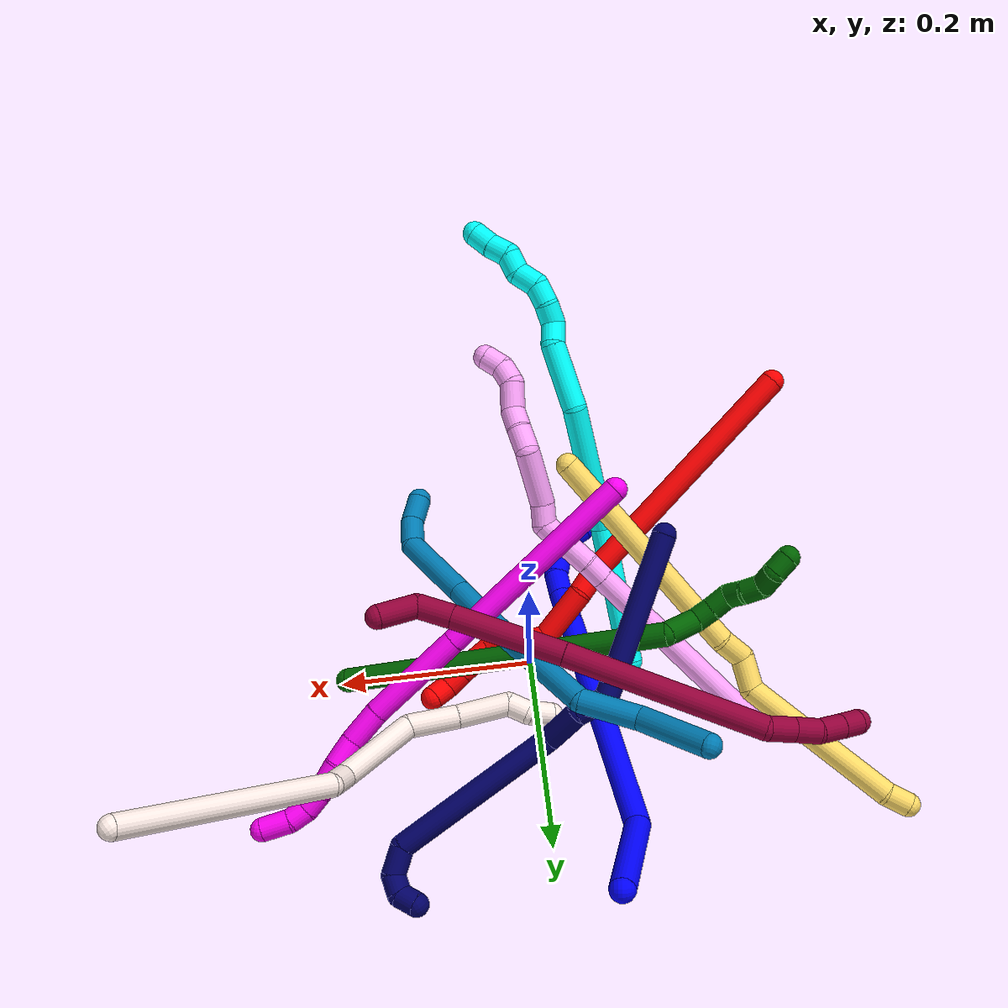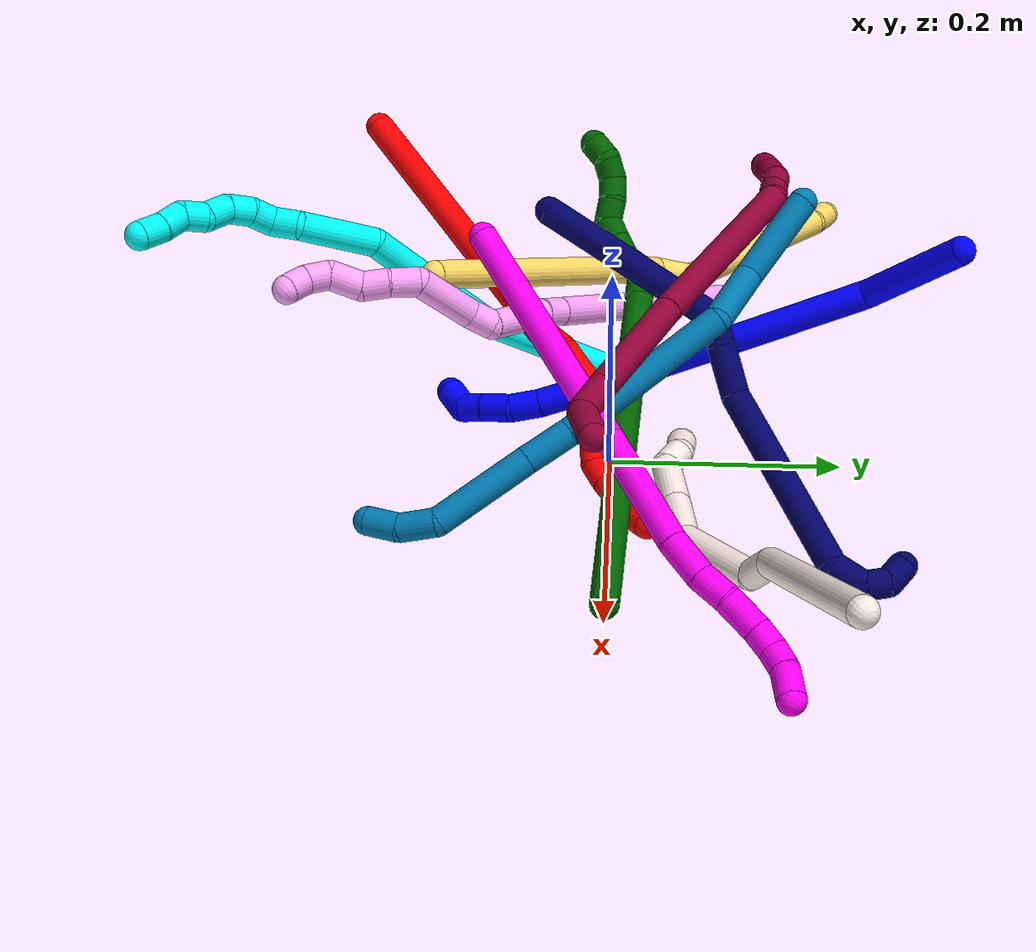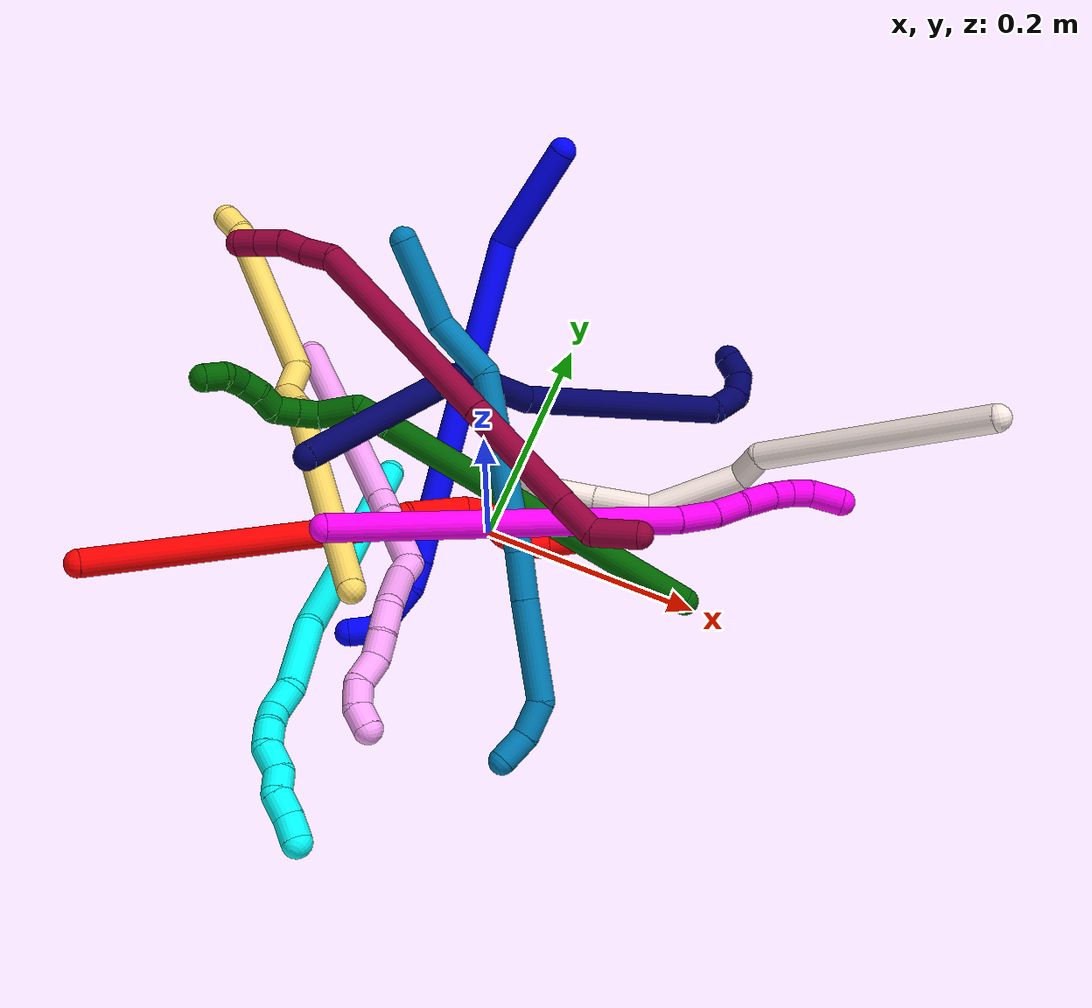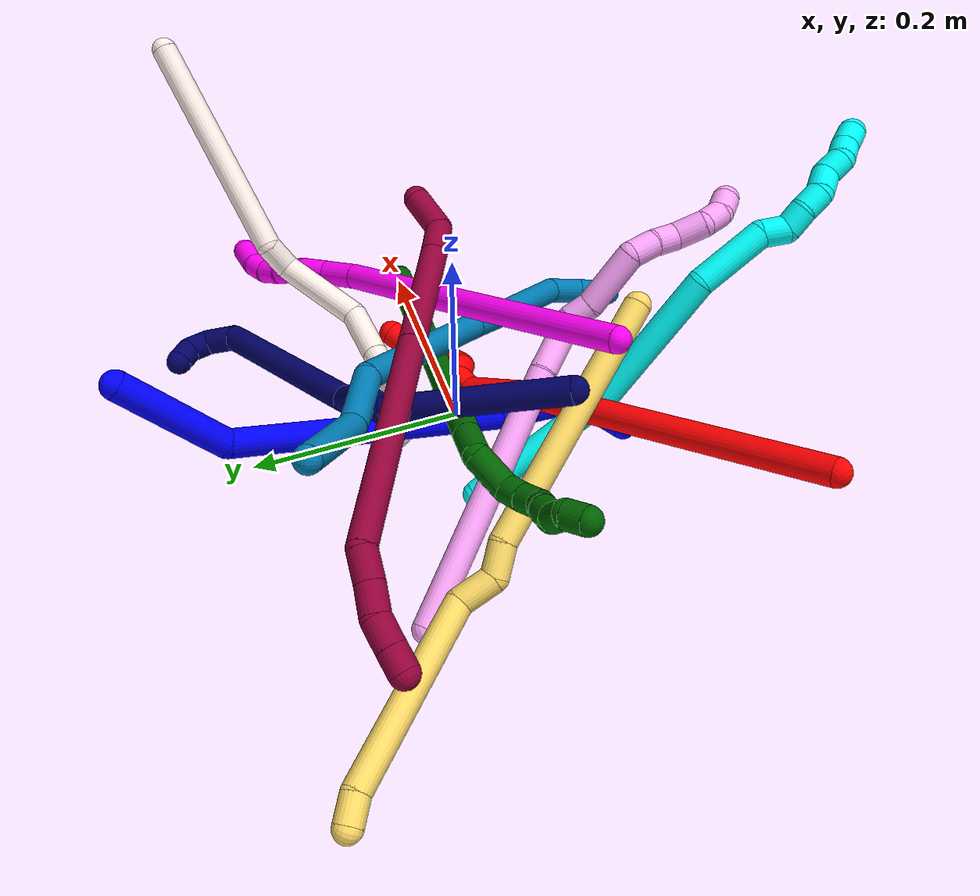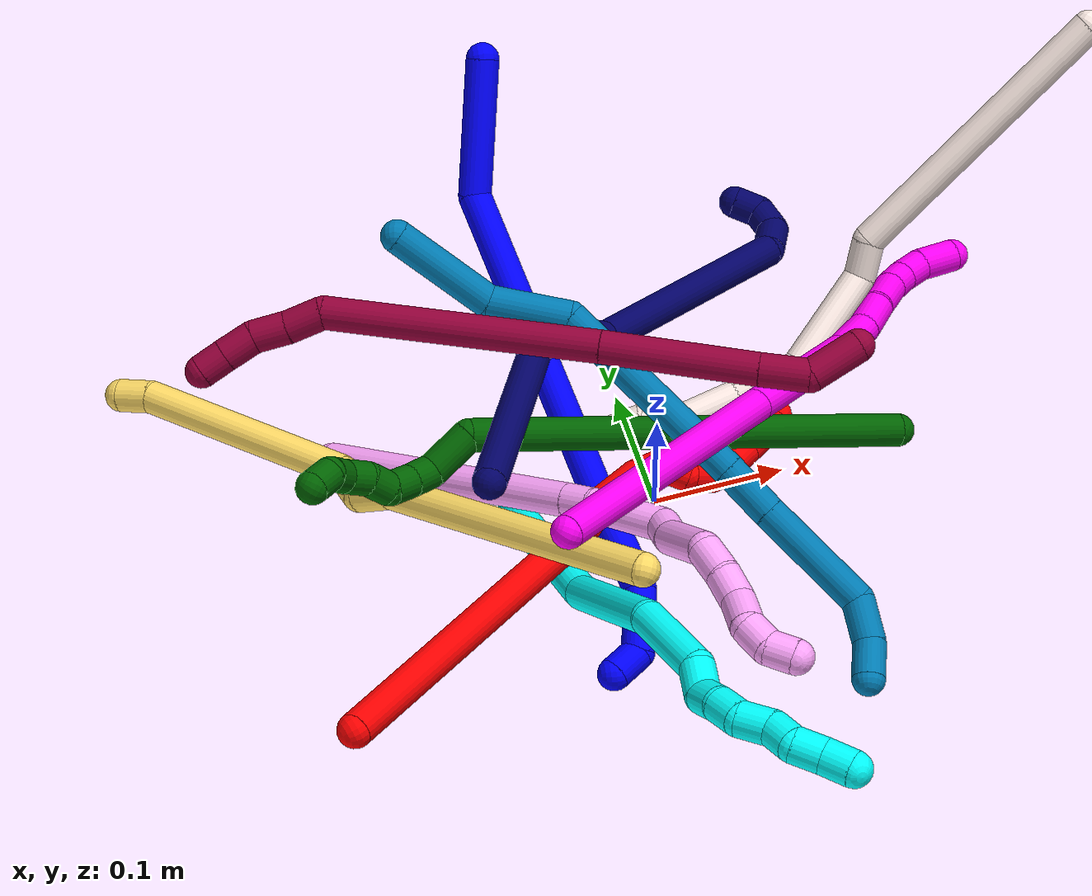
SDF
<sdf version="1.7">
 <world name="default">
  <plugin name="TubeGeneratorPlugin" filename="libtube_generator_plugin.so"/>
  <model name="photoneo_s_sensor">
   <static>1</static>
   <pose>0 0 2 1.57079 1.57079 3.14159</pose>
   <link name="link">
    <inertial><mass>0.1</mass></inertial>
    <sensor name="sensor" type="depth">
     <update_rate>30</update_rate>
     <camera>
      <horizontal_fov>1.22</horizontal_fov>
      <image><width>1920</width><height>1200</height><format>B8G8R8</format></image>
      <clip><near>0.1</near><far>4</far></clip>
      <depth_camera><output>points</output></depth_camera>
     </camera>
     <plugin name="camera_plugin" filename="libgazebo_ros_depth_camera.so">
      <baseline>0.2</baseline>
      <alwaysOn>1</alwaysOn>
      <updateRate>0.0</updateRate>
      <cameraName>camera_ir</cameraName>
      <imageTopicName>/camera/color/image_raw</imageTopicName>
      <cameraInfoTopicName>/camera/color/camera_info</cameraInfoTopicName>
      <depthImageTopicName>/camera/depth/image_raw</depthImageTopicName>
      <depthImageCameraInfoTopicName>/camera/depth/camera_info</depthImageCameraInfoTopicName>
      <pointCloudTopicName>/camera/depth/points</pointCloudTopicName>
      <frameName>fr_optical</frameName>
      <pointCloudCutoff>0.1</pointCloudCutoff>
      <pointCloudCutoffMax>2.0</pointCloudCutoffMax>
      <distortionK1>0</distortionK1>
      <distortionK2>0</distortionK2>
      <distortionK3>0</distortionK3>
      <distortionT1>0</distortionT1>
      <distortionT2>0</distortionT2>
      <CxPrime>0</CxPrime>
      <Cx>0</Cx>
      <Cy>0</Cy>
      <focalLength>0</focalLength>
      <hackBaseline>0</hackBaseline>
     </plugin>
    </sensor>
   </link>
  </model>
  <gravity>0 0 -9.8</gravity>
  <magnetic_field>6e-06 2.3e-05 -4.2e-05</magnetic_field>
  <atmosphere type="adiabatic"/>
  <physics name="default_physics" default="0" type="ode">
   <max_step_size>0.003</max_step_size>
   <real_time_factor>1</real_time_factor>
   <real_time_update_rate>1000</real_time_update_rate>
   <max_contacts>10000</max_contacts>
   <ode>
    <solver>
     <type>quick</type>
     <iters>100</iters>
     <sor>1.3</sor>
     <use_dynamic_moi_rescaling>0</use_dynamic_moi_rescaling>
    </solver>
    <constraints>
     <contact_max_correcting_vel>0</contact_max_correcting_vel>
     <contact_surface_layer>0.001</contact_surface_layer>
     <cfm>0</cfm>
     <erp>0.2</erp>
    </constraints>
   </ode>
  </physics>
  <scene><ambient>0.4 0.4 0.4 1</ambient><background>0.7 0.7 0.7 1</background><shadows>0</shadows></scene>
  <audio><device>default</device></audio>
  <spherical_coordinates>
   <surface_model>EARTH_WGS84</surface_model>
   <latitude_deg>0</latitude_deg>
   <longitude_deg>0</longitude_deg>
   <elevation>0</elevation>
   <heading_deg>0</heading_deg>
  </spherical_coordinates>
  <model name="bin">
   <static>1</static>
   <link name="bottom">
    <collision name="collision-bottom">
     <pose>0 0 -0.01 0 -0 0</pose>
     <geometry><box><size>0.8 0.6 0.02</size></box></geometry>
     <surface>
      <friction><ode><mu>100</mu><mu2>100</mu2></ode></friction>
      <contact><collide_bitmask>65535</collide_bitmask></contact>
     </surface>
    </collision>
   </link>
   <link name="west_wall">
    <collision name="collision-west_wall">
     <pose>-0.41 0 0.1 0 -0 0</pose>
     <geometry><box><size>0.02 0.6 0.2</size></box></geometry>
     <surface>
      <friction><ode><mu>100</mu><mu2>100</mu2></ode></friction>
      <contact><collide_bitmask>65535</collide_bitmask></contact>
     </surface>
    </collision>
   </link>
   <link name="east_wall">
    <collision name="collision-east_wall">
     <pose>0.41 0 0.1 0 -0 0</pose>
     <geometry><box><size>0.02 0.6 0.2</size></box></geometry>
     <surface>
      <friction><ode><mu>100</mu><mu2>100</mu2></ode></friction>
      <contact><collide_bitmask>65535</collide_bitmask></contact>
     </surface>
    </collision>
   </link>
   <link name="south_wall">
    <collision name="collision-south_wall">
     <pose>0 -0.31 0.1 0 -0 0</pose>
     <geometry><box><size>0.8 0.02 0.2</size></box></geometry>
     <surface>
      <friction><ode><mu>100</mu><mu2>100</mu2></ode></friction>
      <contact><collide_bitmask>65535</collide_bitmask></contact>
     </surface>
    </collision>
   </link>
   <link name="north_wall">
    <collision name="collision-north_wall">
     <pose>0 0.31 0.1 0 -0 0</pose>
     <geometry><box><size>0.8 0.02 0.2</size></box></geometry>
     <surface>
      <friction><ode><mu>100</mu><mu2>100</mu2></ode></friction>
      <contact><collide_bitmask>65535</collide_bitmask></contact>
     </surface>
    </collision>
   </link>
  </model>
  <model name="1">
   <static>0</static>
   <link name="1">
    <collision name="collision-cylinder-e_1_1_4">
     <pose>0.016043 -0.047794 -0.00808 1.73828 0.319622 0.376921</pose>
     <geometry><cylinder><radius>0.0125</radius><length>0.102115</length></cylinder></geometry>
     <surface>
      <friction><ode><mu>1.16</mu><mu2>1.16</mu2><slip1>0</slip1><slip2>0</slip2></ode></friction>
      <contact><ode><kp>1e+06</kp><kd>1</kd><max_vel>0</max_vel><min_depth>0.001</min_depth></ode></contact>
     </surface>
    </collision>
    <visual name="visual-cylinder-e_1_1_4">
     <pose>0.016043 -0.047794 -0.00808 1.73828 0.319622 0.376921</pose>
     <geometry><cylinder><radius>0.0125</radius><length>0.102115</length></cylinder></geometry>
     <material><ambient>0 0 1 1</ambient></material>
    </visual>
    <collision name="collision-cylinder-e_2_4_5">
     <pose>0.022549 -0.22218 0.013953 1.33726 -0.073152 -0.057802</pose>
     <geometry><cylinder><radius>0.0125</radius><length>0.260949</length></cylinder></geometry>
     <surface>
      <friction><ode><mu>1.16</mu><mu2>1.16</mu2><slip1>0</slip1><slip2>0</slip2></ode></friction>
      <contact><ode><kp>1e+06</kp><kd>1</kd><max_vel>0</max_vel><min_depth>0.001</min_depth></ode></contact>
     </surface>
    </collision>
    <visual name="visual-cylinder-e_2_4_5">
     <pose>0.022549 -0.22218 0.013953 1.33726 -0.073152 -0.057802</pose>
     <geometry><cylinder><radius>0.0125</radius><length>0.260949</length></cylinder></geometry>
     <material><ambient>0 0 1 1</ambient></material>
    </visual>
    <collision name="collision-cylinder-e_3_5_6">
     <pose>0.010243 -0.367124 0.049175 1.29935 -0.144421 -0.109796</pose>
     <geometry><cylinder><radius>0.0125</radius><length>0.038497</length></cylinder></geometry>
     <surface>
      <friction><ode><mu>1.16</mu><mu2>1.16</mu2><slip1>0</slip1><slip2>0</slip2></ode></friction>
      <contact><ode><kp>1e+06</kp><kd>1</kd><max_vel>0</max_vel><min_depth>0.001</min_depth></ode></contact>
     </surface>
    </collision>
    <visual name="visual-cylinder-e_3_5_6">
     <pose>0.010243 -0.367124 0.049175 1.29935 -0.144421 -0.109796</pose>
     <geometry><cylinder><radius>0.0125</radius><length>0.038497</length></cylinder></geometry>
     <material><ambient>0 0 1 1</ambient></material>
    </visual>
    <collision name="collision-cylinder-e_4_6_7">
     <pose>0.004429 -0.397647 0.05681 1.36604 -0.240098 -0.195678</pose>
     <geometry><cylinder><radius>0.0125</radius><length>0.025599</length></cylinder></geometry>
     <surface>
      <friction><ode><mu>1.16</mu><mu2>1.16</mu2><slip1>0</slip1><slip2>0</slip2></ode></friction>
      <contact><ode><kp>1e+06</kp><kd>1</kd><max_vel>0</max_vel><min_depth>0.001</min_depth></ode></contact>
     </surface>
    </collision>
    <visual name="visual-cylinder-e_4_6_7">
     <pose>0.004429 -0.397647 0.05681 1.36604 -0.240098 -0.195678</pose>
     <geometry><cylinder><radius>0.0125</radius><length>0.025599</length></cylinder></geometry>
     <material><ambient>0 0 1 1</ambient></material>
    </visual>
    <collision name="collision-cylinder-e_5_7_8">
     <pose>-0.000951 -0.422441 0.057045 1.75047 -0.180169 -0.215588</pose>
     <geometry><cylinder><radius>0.0125</radius><length>0.026078</length></cylinder></geometry>
     <surface>
      <friction><ode><mu>1.16</mu><mu2>1.16</mu2><slip1>0</slip1><slip2>0</slip2></ode></friction>
      <contact><ode><kp>1e+06</kp><kd>1</kd><max_vel>0</max_vel><min_depth>0.001</min_depth></ode></contact>
     </surface>
    </collision>
    <visual name="visual-cylinder-e_5_7_8">
     <pose>-0.000951 -0.422441 0.057045 1.75047 -0.180169 -0.215588</pose>
     <geometry><cylinder><radius>0.0125</radius><length>0.026078</length></cylinder></geometry>
     <material><ambient>0 0 1 1</ambient></material>
    </visual>
    <collision name="collision-cylinder-e_6_8_9">
     <pose>-0.003954 -0.445687 0.052511 1.7788 -0.061329 -0.075612</pose>
     <geometry><cylinder><radius>0.0125</radius><length>0.021758</length></cylinder></geometry>
     <surface>
      <friction><ode><mu>1.16</mu><mu2>1.16</mu2><slip1>0</slip1><slip2>0</slip2></ode></friction>
      <contact><ode><kp>1e+06</kp><kd>1</kd><max_vel>0</max_vel><min_depth>0.001</min_depth></ode></contact>
     </surface>
    </collision>
    <visual name="visual-cylinder-e_6_8_9">
     <pose>-0.003954 -0.445687 0.052511 1.7788 -0.061329 -0.075612</pose>
     <geometry><cylinder><radius>0.0125</radius><length>0.021758</length></cylinder></geometry>
     <material><ambient>0 0 1 1</ambient></material>
    </visual>
    <collision name="collision-cylinder-e_7_9_2">
     <pose>-0.007538 -0.463118 0.040195 2.54739 -0.2355 -0.737433</pose>
     <geometry><cylinder><radius>0.0125</radius><length>0.025003</length></cylinder></geometry>
     <surface>
      <friction><ode><mu>1.16</mu><mu2>1.16</mu2><slip1>0</slip1><slip2>0</slip2></ode></friction>
      <contact><ode><kp>1e+06</kp><kd>1</kd><max_vel>0</max_vel><min_depth>0.001</min_depth></ode></contact>
     </surface>
    </collision>
    <visual name="visual-cylinder-e_7_9_2">
     <pose>-0.007538 -0.463118 0.040195 2.54739 -0.2355 -0.737433</pose>
     <geometry><cylinder><radius>0.0125</radius><length>0.025003</length></cylinder></geometry>
     <material><ambient>0 0 1 1</ambient></material>
    </visual>
    <collision name="collision-sphere-2">
     <pose>-0.010455 -0.469924 0.030122 0 -0 0</pose>
     <geometry><sphere><radius>0.0125</radius></sphere></geometry>
     <surface>
      <friction><ode><mu>1.16</mu><mu2>1.16</mu2><slip1>0</slip1><slip2>0</slip2></ode></friction>
      <contact><ode><kp>1e+06</kp><kd>1</kd><max_vel>0</max_vel><min_depth>0.001</min_depth></ode></contact>
     </surface>
    </collision>
    <visual name="visual-sphere-2">
     <pose>-0.010455 -0.469924 0.030122 0 -0 0</pose>
     <geometry><sphere><radius>0.0125</radius></sphere></geometry>
     <material><ambient>0 0 1 1</ambient></material>
    </visual>
    <collision name="collision-sphere-9">
     <pose>-0.004621 -0.456312 0.050268 0 -0 0</pose>
     <geometry><sphere><radius>0.0125</radius></sphere></geometry>
     <surface>
      <friction><ode><mu>1.16</mu><mu2>1.16</mu2><slip1>0</slip1><slip2>0</slip2></ode></friction>
      <contact><ode><kp>1e+06</kp><kd>1</kd><max_vel>0</max_vel><min_depth>0.001</min_depth></ode></contact>
     </surface>
    </collision>
    <visual name="visual-sphere-9">
     <pose>-0.004621 -0.456312 0.050268 0 -0 0</pose>
     <geometry><sphere><radius>0.0125</radius></sphere></geometry>
     <material><ambient>0 0 1 1</ambient></material>
    </visual>
    <collision name="collision-sphere-4">
     <pose>0.032085 -0.095587 -0.016161 0 -0 0</pose>
     <geometry><sphere><radius>0.0125</radius></sphere></geometry>
     <surface>
      <friction><ode><mu>1.16</mu><mu2>1.16</mu2><slip1>0</slip1><slip2>0</slip2></ode></friction>
      <contact><ode><kp>1e+06</kp><kd>1</kd><max_vel>0</max_vel><min_depth>0.001</min_depth></ode></contact>
     </surface>
    </collision>
    <visual name="visual-sphere-4">
     <pose>0.032085 -0.095587 -0.016161 0 -0 0</pose>
     <geometry><sphere><radius>0.0125</radius></sphere></geometry>
     <material><ambient>0 0 1 1</ambient></material>
    </visual>
    <collision name="collision-sphere-1">
     <geometry><sphere><radius>0.0125</radius></sphere></geometry>
     <surface>
      <friction><ode><mu>1.16</mu><mu2>1.16</mu2><slip1>0</slip1><slip2>0</slip2></ode></friction>
      <contact><ode><kp>1e+06</kp><kd>1</kd><max_vel>0</max_vel><min_depth>0.001</min_depth></ode></contact>
     </surface>
    </collision>
    <visual name="visual-sphere-1">
     <geometry><sphere><radius>0.0125</radius></sphere></geometry>
     <material><ambient>0 0 1 1</ambient></material>
    </visual>
    <collision name="collision-sphere-8">
     <pose>-0.003287 -0.435063 0.054753 0 -0 0</pose>
     <geometry><sphere><radius>0.0125</radius></sphere></geometry>
     <surface>
      <friction><ode><mu>1.16</mu><mu2>1.16</mu2><slip1>0</slip1><slip2>0</slip2></ode></friction>
      <contact><ode><kp>1e+06</kp><kd>1</kd><max_vel>0</max_vel><min_depth>0.001</min_depth></ode></contact>
     </surface>
    </collision>
    <visual name="visual-sphere-8">
     <pose>-0.003287 -0.435063 0.054753 0 -0 0</pose>
     <geometry><sphere><radius>0.0125</radius></sphere></geometry>
     <material><ambient>0 0 1 1</ambient></material>
    </visual>
    <collision name="collision-sphere-5">
     <pose>0.013013 -0.348773 0.044068 0 -0 0</pose>
     <geometry><sphere><radius>0.0125</radius></sphere></geometry>
     <surface>
      <friction><ode><mu>1.16</mu><mu2>1.16</mu2><slip1>0</slip1><slip2>0</slip2></ode></friction>
      <contact><ode><kp>1e+06</kp><kd>1</kd><max_vel>0</max_vel><min_depth>0.001</min_depth></ode></contact>
     </surface>
    </collision>
    <visual name="visual-sphere-5">
     <pose>0.013013 -0.348773 0.044068 0 -0 0</pose>
     <geometry><sphere><radius>0.0125</radius></sphere></geometry>
     <material><ambient>0 0 1 1</ambient></material>
    </visual>
    <collision name="collision-sphere-6">
     <pose>0.007473 -0.385475 0.054282 0 -0 0</pose>
     <geometry><sphere><radius>0.0125</radius></sphere></geometry>
     <surface>
      <friction><ode><mu>1.16</mu><mu2>1.16</mu2><slip1>0</slip1><slip2>0</slip2></ode></friction>
      <contact><ode><kp>1e+06</kp><kd>1</kd><max_vel>0</max_vel><min_depth>0.001</min_depth></ode></contact>
     </surface>
    </collision>
    <visual name="visual-sphere-6">
     <pose>0.007473 -0.385475 0.054282 0 -0 0</pose>
     <geometry><sphere><radius>0.0125</radius></sphere></geometry>
     <material><ambient>0 0 1 1</ambient></material>
    </visual>
    <collision name="collision-sphere-7">
     <pose>0.001386 -0.40982 0.059338 0 -0 0</pose>
     <geometry><sphere><radius>0.0125</radius></sphere></geometry>
     <surface>
      <friction><ode><mu>1.16</mu><mu2>1.16</mu2><slip1>0</slip1><slip2>0</slip2></ode></friction>
      <contact><ode><kp>1e+06</kp><kd>1</kd><max_vel>0</max_vel><min_depth>0.001</min_depth></ode></contact>
     </surface>
    </collision>
    <visual name="visual-sphere-7">
     <pose>0.001386 -0.40982 0.059338 0 -0 0</pose>
     <geometry><sphere><radius>0.0125</radius></sphere></geometry>
     <material><ambient>0 0 1 1</ambient></material>
    </visual>
    <inertial>
     <pose>0.015462 -0.238928 0.019597 0 -0 0</pose>
     <mass>0.5</mass>
     <inertia>
      <ixx>0.001523</ixx>
      <ixy>0</ixy>
      <ixz>0</ixz>
      <iyy>0.000254</iyy>
      <iyz>0</iyz>
      <izz>0.001632</izz>
     </inertia>
    </inertial>
   </link>
   <pose>-0.047521 0.288523 0.199749 1.70038 1.1381 1.57814</pose>
  </model>
  <model name="2">
   <static>0</static>
   <link name="2">
    <collision name="collision-cylinder-e_1_1_4">
     <pose>0.064474 0.018713 -0.115229 -2.9806 0.504599 -2.53504</pose>
     <geometry><cylinder><radius>0.0125</radius><length>0.266719</length></cylinder></geometry>
     <surface>
      <friction><ode><mu>1.16</mu><mu2>1.16</mu2><slip1>0</slip1><slip2>0</slip2></ode></friction>
      <contact><ode><kp>1e+06</kp><kd>1</kd><max_vel>0</max_vel><min_depth>0.001</min_depth></ode></contact>
     </surface>
    </collision>
    <visual name="visual-cylinder-e_1_1_4">
     <pose>0.064474 0.018713 -0.115229 -2.9806 0.504599 -2.53504</pose>
     <geometry><cylinder><radius>0.0125</radius><length>0.266719</length></cylinder></geometry>
     <material><ambient>1 0 0 1</ambient></material>
    </visual>
    <collision name="collision-cylinder-e_2_4_5">
     <pose>0.137267 0.036922 -0.241973 3.09782 0.625258 3.00635</pose>
     <geometry><cylinder><radius>0.0125</radius><length>0.02843</length></cylinder></geometry>
     <surface>
      <friction><ode><mu>1.16</mu><mu2>1.16</mu2><slip1>0</slip1><slip2>0</slip2></ode></friction>
      <contact><ode><kp>1e+06</kp><kd>1</kd><max_vel>0</max_vel><min_depth>0.001</min_depth></ode></contact>
     </surface>
    </collision>
    <visual name="visual-cylinder-e_2_4_5">
     <pose>0.137267 0.036922 -0.241973 3.09782 0.625258 3.00635</pose>
     <geometry><cylinder><radius>0.0125</radius><length>0.02843</length></cylinder></geometry>
     <material><ambient>1 0 0 1</ambient></material>
    </visual>
    <collision name="collision-cylinder-e_3_5_6">
     <pose>0.161781 0.043873 -0.276253 -2.82509 0.59444 -2.18095</pose>
     <geometry><cylinder><radius>0.0125</radius><length>0.05783</length></cylinder></geometry>
     <surface>
      <friction><ode><mu>1.16</mu><mu2>1.16</mu2><slip1>0</slip1><slip2>0</slip2></ode></friction>
      <contact><ode><kp>1e+06</kp><kd>1</kd><max_vel>0</max_vel><min_depth>0.001</min_depth></ode></contact>
     </surface>
    </collision>
    <visual name="visual-cylinder-e_3_5_6">
     <pose>0.161781 0.043873 -0.276253 -2.82509 0.59444 -2.18095</pose>
     <geometry><cylinder><radius>0.0125</radius><length>0.05783</length></cylinder></geometry>
     <material><ambient>1 0 0 1</ambient></material>
    </visual>
    <collision name="collision-cylinder-e_4_6_7">
     <pose>0.17847 0.052988 -0.309787 -2.98877 0.045438 -0.577021</pose>
     <geometry><cylinder><radius>0.0125</radius><length>0.021814</length></cylinder></geometry>
     <surface>
      <friction><ode><mu>1.16</mu><mu2>1.16</mu2><slip1>0</slip1><slip2>0</slip2></ode></friction>
      <contact><ode><kp>1e+06</kp><kd>1</kd><max_vel>0</max_vel><min_depth>0.001</min_depth></ode></contact>
     </surface>
    </collision>
    <visual name="visual-cylinder-e_4_6_7">
     <pose>0.17847 0.052988 -0.309787 -2.98877 0.045438 -0.577021</pose>
     <geometry><cylinder><radius>0.0125</radius><length>0.021814</length></cylinder></geometry>
     <material><ambient>1 0 0 1</ambient></material>
    </visual>
    <collision name="collision-cylinder-e_5_7_8">
     <pose>0.174332 0.060816 -0.327618 -2.4235 -0.45897 1.11347</pose>
     <geometry><cylinder><radius>0.0125</radius><length>0.020919</length></cylinder></geometry>
     <surface>
      <friction><ode><mu>1.16</mu><mu2>1.16</mu2><slip1>0</slip1><slip2>0</slip2></ode></friction>
      <contact><ode><kp>1e+06</kp><kd>1</kd><max_vel>0</max_vel><min_depth>0.001</min_depth></ode></contact>
     </surface>
    </collision>
    <visual name="visual-cylinder-e_5_7_8">
     <pose>0.174332 0.060816 -0.327618 -2.4235 -0.45897 1.11347</pose>
     <geometry><cylinder><radius>0.0125</radius><length>0.020919</length></cylinder></geometry>
     <material><ambient>1 0 0 1</ambient></material>
    </visual>
    <collision name="collision-cylinder-e_6_8_9">
     <pose>0.1714 0.073988 -0.34406 -2.50038 0.144388 -0.428885</pose>
     <geometry><cylinder><radius>0.0125</radius><length>0.023657</length></cylinder></geometry>
     <surface>
      <friction><ode><mu>1.16</mu><mu2>1.16</mu2><slip1>0</slip1><slip2>0</slip2></ode></friction>
      <contact><ode><kp>1e+06</kp><kd>1</kd><max_vel>0</max_vel><min_depth>0.001</min_depth></ode></contact>
     </surface>
    </collision>
    <visual name="visual-cylinder-e_6_8_9">
     <pose>0.1714 0.073988 -0.34406 -2.50038 0.144388 -0.428885</pose>
     <geometry><cylinder><radius>0.0125</radius><length>0.023657</length></cylinder></geometry>
     <material><ambient>1 0 0 1</ambient></material>
    </visual>
    <collision name="collision-cylinder-e_7_9_10">
     <pose>0.17695 0.082624 -0.36261 -2.96516 0.391759 -2.30298</pose>
     <geometry><cylinder><radius>0.0125</radius><length>0.020157</length></cylinder></geometry>
     <surface>
      <friction><ode><mu>1.16</mu><mu2>1.16</mu2><slip1>0</slip1><slip2>0</slip2></ode></friction>
      <contact><ode><kp>1e+06</kp><kd>1</kd><max_vel>0</max_vel><min_depth>0.001</min_depth></ode></contact>
     </surface>
    </collision>
    <visual name="visual-cylinder-e_7_9_10">
     <pose>0.17695 0.082624 -0.36261 -2.96516 0.391759 -2.30298</pose>
     <geometry><cylinder><radius>0.0125</radius><length>0.020157</length></cylinder></geometry>
     <material><ambient>1 0 0 1</ambient></material>
    </visual>
    <collision name="collision-cylinder-e_8_10_11">
     <pose>0.1851 0.08487 -0.380947 -3.0751 0.437965 -2.84491</pose>
     <geometry><cylinder><radius>0.0125</radius><length>0.020289</length></cylinder></geometry>
     <surface>
      <friction><ode><mu>1.16</mu><mu2>1.16</mu2><slip1>0</slip1><slip2>0</slip2></ode></friction>
      <contact><ode><kp>1e+06</kp><kd>1</kd><max_vel>0</max_vel><min_depth>0.001</min_depth></ode></contact>
     </surface>
    </collision>
    <visual name="visual-cylinder-e_8_10_11">
     <pose>0.1851 0.08487 -0.380947 -3.0751 0.437965 -2.84491</pose>
     <geometry><cylinder><radius>0.0125</radius><length>0.020289</length></cylinder></geometry>
     <material><ambient>1 0 0 1</ambient></material>
    </visual>
    <collision name="collision-cylinder-e_9_11_12">
     <pose>0.193644 0.086103 -0.399176 -3.07293 0.436818 -2.83453</pose>
     <geometry><cylinder><radius>0.0125</radius><length>0.02005</length></cylinder></geometry>
     <surface>
      <friction><ode><mu>1.16</mu><mu2>1.16</mu2><slip1>0</slip1><slip2>0</slip2></ode></friction>
      <contact><ode><kp>1e+06</kp><kd>1</kd><max_vel>0</max_vel><min_depth>0.001</min_depth></ode></contact>
     </surface>
    </collision>
    <visual name="visual-cylinder-e_9_11_12">
     <pose>0.193644 0.086103 -0.399176 -3.07293 0.436818 -2.83453</pose>
     <geometry><cylinder><radius>0.0125</radius><length>0.02005</length></cylinder></geometry>
     <material><ambient>1 0 0 1</ambient></material>
    </visual>
    <collision name="collision-cylinder-e_10_12_2">
     <pose>0.200362 0.083835 -0.417557 2.84071 0.248671 1.37897</pose>
     <geometry><cylinder><radius>0.0125</radius><length>0.020134</length></cylinder></geometry>
     <surface>
      <friction><ode><mu>1.16</mu><mu2>1.16</mu2><slip1>0</slip1><slip2>0</slip2></ode></friction>
      <contact><ode><kp>1e+06</kp><kd>1</kd><max_vel>0</max_vel><min_depth>0.001</min_depth></ode></contact>
     </surface>
    </collision>
    <visual name="visual-cylinder-e_10_12_2">
     <pose>0.200362 0.083835 -0.417557 2.84071 0.248671 1.37897</pose>
     <geometry><cylinder><radius>0.0125</radius><length>0.020134</length></cylinder></geometry>
     <material><ambient>1 0 0 1</ambient></material>
    </visual>
    <collision name="collision-sphere-2">
     <pose>0.20284 0.080943 -0.426877 0 -0 0</pose>
     <geometry><sphere><radius>0.0125</radius></sphere></geometry>
     <surface>
      <friction><ode><mu>1.16</mu><mu2>1.16</mu2><slip1>0</slip1><slip2>0</slip2></ode></friction>
      <contact><ode><kp>1e+06</kp><kd>1</kd><max_vel>0</max_vel><min_depth>0.001</min_depth></ode></contact>
     </surface>
    </collision>
    <visual name="visual-sphere-2">
     <pose>0.20284 0.080943 -0.426877 0 -0 0</pose>
     <geometry><sphere><radius>0.0125</radius></sphere></geometry>
     <material><ambient>1 0 0 1</ambient></material>
    </visual>
    <collision name="collision-sphere-12">
     <pose>0.197885 0.086727 -0.408238 0 -0 0</pose>
     <geometry><sphere><radius>0.0125</radius></sphere></geometry>
     <surface>
      <friction><ode><mu>1.16</mu><mu2>1.16</mu2><slip1>0</slip1><slip2>0</slip2></ode></friction>
      <contact><ode><kp>1e+06</kp><kd>1</kd><max_vel>0</max_vel><min_depth>0.001</min_depth></ode></contact>
     </surface>
    </collision>
    <visual name="visual-sphere-12">
     <pose>0.197885 0.086727 -0.408238 0 -0 0</pose>
     <geometry><sphere><radius>0.0125</radius></sphere></geometry>
     <material><ambient>1 0 0 1</ambient></material>
    </visual>
    <collision name="collision-sphere-11">
     <pose>0.189403 0.08548 -0.390114 0 -0 0</pose>
     <geometry><sphere><radius>0.0125</radius></sphere></geometry>
     <surface>
      <friction><ode><mu>1.16</mu><mu2>1.16</mu2><slip1>0</slip1><slip2>0</slip2></ode></friction>
      <contact><ode><kp>1e+06</kp><kd>1</kd><max_vel>0</max_vel><min_depth>0.001</min_depth></ode></contact>
     </surface>
    </collision>
    <visual name="visual-sphere-11">
     <pose>0.189403 0.08548 -0.390114 0 -0 0</pose>
     <geometry><sphere><radius>0.0125</radius></sphere></geometry>
     <material><ambient>1 0 0 1</ambient></material>
    </visual>
    <collision name="collision-sphere-10">
     <pose>0.180798 0.084259 -0.371781 0 -0 0</pose>
     <geometry><sphere><radius>0.0125</radius></sphere></geometry>
     <surface>
      <friction><ode><mu>1.16</mu><mu2>1.16</mu2><slip1>0</slip1><slip2>0</slip2></ode></friction>
      <contact><ode><kp>1e+06</kp><kd>1</kd><max_vel>0</max_vel><min_depth>0.001</min_depth></ode></contact>
     </surface>
    </collision>
    <visual name="visual-sphere-10">
     <pose>0.180798 0.084259 -0.371781 0 -0 0</pose>
     <geometry><sphere><radius>0.0125</radius></sphere></geometry>
     <material><ambient>1 0 0 1</ambient></material>
    </visual>
    <collision name="collision-sphere-9">
     <pose>0.173102 0.080989 -0.35344 0 -0 0</pose>
     <geometry><sphere><radius>0.0125</radius></sphere></geometry>
     <surface>
      <friction><ode><mu>1.16</mu><mu2>1.16</mu2><slip1>0</slip1><slip2>0</slip2></ode></friction>
      <contact><ode><kp>1e+06</kp><kd>1</kd><max_vel>0</max_vel><min_depth>0.001</min_depth></ode></contact>
     </surface>
    </collision>
    <visual name="visual-sphere-9">
     <pose>0.173102 0.080989 -0.35344 0 -0 0</pose>
     <geometry><sphere><radius>0.0125</radius></sphere></geometry>
     <material><ambient>1 0 0 1</ambient></material>
    </visual>
    <collision name="collision-sphere-4">
     <pose>0.128947 0.037426 -0.230459 0 -0 0</pose>
     <geometry><sphere><radius>0.0125</radius></sphere></geometry>
     <surface>
      <friction><ode><mu>1.16</mu><mu2>1.16</mu2><slip1>0</slip1><slip2>0</slip2></ode></friction>
      <contact><ode><kp>1e+06</kp><kd>1</kd><max_vel>0</max_vel><min_depth>0.001</min_depth></ode></contact>
     </surface>
    </collision>
    <visual name="visual-sphere-4">
     <pose>0.128947 0.037426 -0.230459 0 -0 0</pose>
     <geometry><sphere><radius>0.0125</radius></sphere></geometry>
     <material><ambient>1 0 0 1</ambient></material>
    </visual>
    <collision name="collision-sphere-1">
     <geometry><sphere><radius>0.0125</radius></sphere></geometry>
     <surface>
      <friction><ode><mu>1.16</mu><mu2>1.16</mu2><slip1>0</slip1><slip2>0</slip2></ode></friction>
      <contact><ode><kp>1e+06</kp><kd>1</kd><max_vel>0</max_vel><min_depth>0.001</min_depth></ode></contact>
     </surface>
    </collision>
    <visual name="visual-sphere-1">
     <geometry><sphere><radius>0.0125</radius></sphere></geometry>
     <material><ambient>1 0 0 1</ambient></material>
    </visual>
    <collision name="collision-sphere-8">
     <pose>0.169698 0.066986 -0.33468 0 -0 0</pose>
     <geometry><sphere><radius>0.0125</radius></sphere></geometry>
     <surface>
      <friction><ode><mu>1.16</mu><mu2>1.16</mu2><slip1>0</slip1><slip2>0</slip2></ode></friction>
      <contact><ode><kp>1e+06</kp><kd>1</kd><max_vel>0</max_vel><min_depth>0.001</min_depth></ode></contact>
     </surface>
    </collision>
    <visual name="visual-sphere-8">
     <pose>0.169698 0.066986 -0.33468 0 -0 0</pose>
     <geometry><sphere><radius>0.0125</radius></sphere></geometry>
     <material><ambient>1 0 0 1</ambient></material>
    </visual>
    <collision name="collision-sphere-5">
     <pose>0.145587 0.036418 -0.253488 0 -0 0</pose>
     <geometry><sphere><radius>0.0125</radius></sphere></geometry>
     <surface>
      <friction><ode><mu>1.16</mu><mu2>1.16</mu2><slip1>0</slip1><slip2>0</slip2></ode></friction>
      <contact><ode><kp>1e+06</kp><kd>1</kd><max_vel>0</max_vel><min_depth>0.001</min_depth></ode></contact>
     </surface>
    </collision>
    <visual name="visual-sphere-5">
     <pose>0.145587 0.036418 -0.253488 0 -0 0</pose>
     <geometry><sphere><radius>0.0125</radius></sphere></geometry>
     <material><ambient>1 0 0 1</ambient></material>
    </visual>
    <collision name="collision-sphere-6">
     <pose>0.177975 0.051329 -0.299018 0 -0 0</pose>
     <geometry><sphere><radius>0.0125</radius></sphere></geometry>
     <surface>
      <friction><ode><mu>1.16</mu><mu2>1.16</mu2><slip1>0</slip1><slip2>0</slip2></ode></friction>
      <contact><ode><kp>1e+06</kp><kd>1</kd><max_vel>0</max_vel><min_depth>0.001</min_depth></ode></contact>
     </surface>
    </collision>
    <visual name="visual-sphere-6">
     <pose>0.177975 0.051329 -0.299018 0 -0 0</pose>
     <geometry><sphere><radius>0.0125</radius></sphere></geometry>
     <material><ambient>1 0 0 1</ambient></material>
    </visual>
    <collision name="collision-sphere-7">
     <pose>0.178966 0.054647 -0.320556 0 -0 0</pose>
     <geometry><sphere><radius>0.0125</radius></sphere></geometry>
     <surface>
      <friction><ode><mu>1.16</mu><mu2>1.16</mu2><slip1>0</slip1><slip2>0</slip2></ode></friction>
      <contact><ode><kp>1e+06</kp><kd>1</kd><max_vel>0</max_vel><min_depth>0.001</min_depth></ode></contact>
     </surface>
    </collision>
    <visual name="visual-sphere-7">
     <pose>0.178966 0.054647 -0.320556 0 -0 0</pose>
     <geometry><sphere><radius>0.0125</radius></sphere></geometry>
     <material><ambient>1 0 0 1</ambient></material>
    </visual>
    <inertial>
     <pose>0.114577 0.039116 -0.213577 0 -0 0</pose>
     <mass>0.5</mass>
     <inertia>
      <ixx>-0.001947</ixx>
      <ixy>0</ixy>
      <ixz>0</ixz>
      <iyy>0.000577</iyy>
      <iyz>0</iyz>
      <izz>-0.001047</izz>
     </inertia>
    </inertial>
   </link>
   <pose>-0.278869 -0.219289 0.158296 -1.6401 0.454084 1.7984</pose>
  </model>
  <model name="3">
   <static>0</static>
   <link name="3">
    <collision name="collision-cylinder-e_1_1_4">
     <pose>0.001 -0.001209 0.072323 0.016713 0.01383 0.000116</pose>
     <geometry><cylinder><radius>0.0125</radius><length>0.144679</length></cylinder></geometry>
     <surface>
      <friction><ode><mu>1.16</mu><mu2>1.16</mu2><slip1>0</slip1><slip2>0</slip2></ode></friction>
      <contact><ode><kp>1e+06</kp><kd>1</kd><max_vel>0</max_vel><min_depth>0.001</min_depth></ode></contact>
     </surface>
    </collision>
    <visual name="visual-cylinder-e_1_1_4">
     <pose>0.001 -0.001209 0.072323 0.016713 0.01383 0.000116</pose>
     <geometry><cylinder><radius>0.0125</radius><length>0.144679</length></cylinder></geometry>
     <material><ambient>0.003922 1 0.996078 1</ambient></material>
    </visual>
    <collision name="collision-cylinder-e_2_4_5">
     <pose>-0.012979 -0.016748 0.208598 0.220437 -0.224708 -0.024972</pose>
     <geometry><cylinder><radius>0.0125</radius><length>0.134458</length></cylinder></geometry>
     <surface>
      <friction><ode><mu>1.16</mu><mu2>1.16</mu2><slip1>0</slip1><slip2>0</slip2></ode></friction>
      <contact><ode><kp>1e+06</kp><kd>1</kd><max_vel>0</max_vel><min_depth>0.001</min_depth></ode></contact>
     </surface>
    </collision>
    <visual name="visual-cylinder-e_2_4_5">
     <pose>-0.012979 -0.016748 0.208598 0.220437 -0.224708 -0.024972</pose>
     <geometry><cylinder><radius>0.0125</radius><length>0.134458</length></cylinder></geometry>
     <material><ambient>0.003922 1 0.996078 1</ambient></material>
    </visual>
    <collision name="collision-cylinder-e_3_5_6">
     <pose>-0.028288 -0.026613 0.306045 -0.13255 -0.009727 0.000646</pose>
     <geometry><cylinder><radius>0.0125</radius><length>0.067584</length></cylinder></geometry>
     <surface>
      <friction><ode><mu>1.16</mu><mu2>1.16</mu2><slip1>0</slip1><slip2>0</slip2></ode></friction>
      <contact><ode><kp>1e+06</kp><kd>1</kd><max_vel>0</max_vel><min_depth>0.001</min_depth></ode></contact>
     </surface>
    </collision>
    <visual name="visual-cylinder-e_3_5_6">
     <pose>-0.028288 -0.026613 0.306045 -0.13255 -0.009727 0.000646</pose>
     <geometry><cylinder><radius>0.0125</radius><length>0.067584</length></cylinder></geometry>
     <material><ambient>0.003922 1 0.996078 1</ambient></material>
    </visual>
    <collision name="collision-cylinder-e_4_6_7">
     <pose>-0.023054 -0.020326 0.349982 -0.172626 0.48331 -0.042647</pose>
     <geometry><cylinder><radius>0.0125</radius><length>0.023942</length></cylinder></geometry>
     <surface>
      <friction><ode><mu>1.16</mu><mu2>1.16</mu2><slip1>0</slip1><slip2>0</slip2></ode></friction>
      <contact><ode><kp>1e+06</kp><kd>1</kd><max_vel>0</max_vel><min_depth>0.001</min_depth></ode></contact>
     </surface>
    </collision>
    <visual name="visual-cylinder-e_4_6_7">
     <pose>-0.023054 -0.020326 0.349982 -0.172626 0.48331 -0.042647</pose>
     <geometry><cylinder><radius>0.0125</radius><length>0.023942</length></cylinder></geometry>
     <material><ambient>0.003922 1 0.996078 1</ambient></material>
    </visual>
    <collision name="collision-cylinder-e_5_7_8">
     <pose>-0.019734 -0.019025 0.370862 0.049718 -0.211426 -0.005277</pose>
     <geometry><cylinder><radius>0.0125</radius><length>0.021378</length></cylinder></geometry>
     <surface>
      <friction><ode><mu>1.16</mu><mu2>1.16</mu2><slip1>0</slip1><slip2>0</slip2></ode></friction>
      <contact><ode><kp>1e+06</kp><kd>1</kd><max_vel>0</max_vel><min_depth>0.001</min_depth></ode></contact>
     </surface>
    </collision>
    <visual name="visual-cylinder-e_5_7_8">
     <pose>-0.019734 -0.019025 0.370862 0.049718 -0.211426 -0.005277</pose>
     <geometry><cylinder><radius>0.0125</radius><length>0.021378</length></cylinder></geometry>
     <material><ambient>0.003922 1 0.996078 1</ambient></material>
    </visual>
    <collision name="collision-cylinder-e_6_8_9">
     <pose>-0.0232 -0.017209 0.391645 -0.22203 -0.114856 0.012817</pose>
     <geometry><cylinder><radius>0.0125</radius><length>0.02135</length></cylinder></geometry>
     <surface>
      <friction><ode><mu>1.16</mu><mu2>1.16</mu2><slip1>0</slip1><slip2>0</slip2></ode></friction>
      <contact><ode><kp>1e+06</kp><kd>1</kd><max_vel>0</max_vel><min_depth>0.001</min_depth></ode></contact>
     </surface>
    </collision>
    <visual name="visual-cylinder-e_6_8_9">
     <pose>-0.0232 -0.017209 0.391645 -0.22203 -0.114856 0.012817</pose>
     <geometry><cylinder><radius>0.0125</radius><length>0.02135</length></cylinder></geometry>
     <material><ambient>0.003922 1 0.996078 1</ambient></material>
    </visual>
    <collision name="collision-cylinder-e_7_9_10">
     <pose>-0.029023 -0.008017 0.410376 -0.68537 -0.401537 0.144955</pose>
     <geometry><cylinder><radius>0.0125</radius><length>0.023538</length></cylinder></geometry>
     <surface>
      <friction><ode><mu>1.16</mu><mu2>1.16</mu2><slip1>0</slip1><slip2>0</slip2></ode></friction>
      <contact><ode><kp>1e+06</kp><kd>1</kd><max_vel>0</max_vel><min_depth>0.001</min_depth></ode></contact>
     </surface>
    </collision>
    <visual name="visual-cylinder-e_7_9_10">
     <pose>-0.029023 -0.008017 0.410376 -0.68537 -0.401537 0.144955</pose>
     <geometry><cylinder><radius>0.0125</radius><length>0.023538</length></cylinder></geometry>
     <material><ambient>0.003922 1 0.996078 1</ambient></material>
    </visual>
    <collision name="collision-cylinder-e_8_10_11">
     <pose>-0.034289 0.001543 0.428608 -0.267935 -0.065148 0.008783</pose>
     <geometry><cylinder><radius>0.0125</radius><length>0.020462</length></cylinder></geometry>
     <surface>
      <friction><ode><mu>1.16</mu><mu2>1.16</mu2><slip1>0</slip1><slip2>0</slip2></ode></friction>
      <contact><ode><kp>1e+06</kp><kd>1</kd><max_vel>0</max_vel><min_depth>0.001</min_depth></ode></contact>
     </surface>
    </collision>
    <visual name="visual-cylinder-e_8_10_11">
     <pose>-0.034289 0.001543 0.428608 -0.267935 -0.065148 0.008783</pose>
     <geometry><cylinder><radius>0.0125</radius><length>0.020462</length></cylinder></geometry>
     <material><ambient>0.003922 1 0.996078 1</ambient></material>
    </visual>
    <collision name="collision-cylinder-e_9_11_12">
     <pose>-0.038225 0.011855 0.445215 -0.844191 -0.3108 0.14048</pose>
     <geometry><cylinder><radius>0.0125</radius><length>0.021384</length></cylinder></geometry>
     <surface>
      <friction><ode><mu>1.16</mu><mu2>1.16</mu2><slip1>0</slip1><slip2>0</slip2></ode></friction>
      <contact><ode><kp>1e+06</kp><kd>1</kd><max_vel>0</max_vel><min_depth>0.001</min_depth></ode></contact>
     </surface>
    </collision>
    <visual name="visual-cylinder-e_9_11_12">
     <pose>-0.038225 0.011855 0.445215 -0.844191 -0.3108 0.14048</pose>
     <geometry><cylinder><radius>0.0125</radius><length>0.021384</length></cylinder></geometry>
     <material><ambient>0.003922 1 0.996078 1</ambient></material>
    </visual>
    <collision name="collision-cylinder-e_10_12_2">
     <pose>-0.044373 0.025764 0.460017 -0.664767 -0.274641 0.095331</pose>
     <geometry><cylinder><radius>0.0125</radius><length>0.021224</length></cylinder></geometry>
     <surface>
      <friction><ode><mu>1.16</mu><mu2>1.16</mu2><slip1>0</slip1><slip2>0</slip2></ode></friction>
      <contact><ode><kp>1e+06</kp><kd>1</kd><max_vel>0</max_vel><min_depth>0.001</min_depth></ode></contact>
     </surface>
    </collision>
    <visual name="visual-cylinder-e_10_12_2">
     <pose>-0.044373 0.025764 0.460017 -0.664767 -0.274641 0.095331</pose>
     <geometry><cylinder><radius>0.0125</radius><length>0.021224</length></cylinder></geometry>
     <material><ambient>0.003922 1 0.996078 1</ambient></material>
    </visual>
    <collision name="collision-sphere-2">
     <pose>-0.047251 0.032065 0.468057 0 -0 0</pose>
     <geometry><sphere><radius>0.0125</radius></sphere></geometry>
     <surface>
      <friction><ode><mu>1.16</mu><mu2>1.16</mu2><slip1>0</slip1><slip2>0</slip2></ode></friction>
      <contact><ode><kp>1e+06</kp><kd>1</kd><max_vel>0</max_vel><min_depth>0.001</min_depth></ode></contact>
     </surface>
    </collision>
    <visual name="visual-sphere-2">
     <pose>-0.047251 0.032065 0.468057 0 -0 0</pose>
     <geometry><sphere><radius>0.0125</radius></sphere></geometry>
     <material><ambient>0.003922 1 0.996078 1</ambient></material>
    </visual>
    <collision name="collision-sphere-12">
     <pose>-0.041495 0.019463 0.451978 0 -0 0</pose>
     <geometry><sphere><radius>0.0125</radius></sphere></geometry>
     <surface>
      <friction><ode><mu>1.16</mu><mu2>1.16</mu2><slip1>0</slip1><slip2>0</slip2></ode></friction>
      <contact><ode><kp>1e+06</kp><kd>1</kd><max_vel>0</max_vel><min_depth>0.001</min_depth></ode></contact>
     </surface>
    </collision>
    <visual name="visual-sphere-12">
     <pose>-0.041495 0.019463 0.451978 0 -0 0</pose>
     <geometry><sphere><radius>0.0125</radius></sphere></geometry>
     <material><ambient>0.003922 1 0.996078 1</ambient></material>
    </visual>
    <collision name="collision-sphere-11">
     <pose>-0.034955 0.004246 0.438452 0 -0 0</pose>
     <geometry><sphere><radius>0.0125</radius></sphere></geometry>
     <surface>
      <friction><ode><mu>1.16</mu><mu2>1.16</mu2><slip1>0</slip1><slip2>0</slip2></ode></friction>
      <contact><ode><kp>1e+06</kp><kd>1</kd><max_vel>0</max_vel><min_depth>0.001</min_depth></ode></contact>
     </surface>
    </collision>
    <visual name="visual-sphere-11">
     <pose>-0.034955 0.004246 0.438452 0 -0 0</pose>
     <geometry><sphere><radius>0.0125</radius></sphere></geometry>
     <material><ambient>0.003922 1 0.996078 1</ambient></material>
    </visual>
    <collision name="collision-sphere-10">
     <pose>-0.033623 -0.00116 0.418763 0 -0 0</pose>
     <geometry><sphere><radius>0.0125</radius></sphere></geometry>
     <surface>
      <friction><ode><mu>1.16</mu><mu2>1.16</mu2><slip1>0</slip1><slip2>0</slip2></ode></friction>
      <contact><ode><kp>1e+06</kp><kd>1</kd><max_vel>0</max_vel><min_depth>0.001</min_depth></ode></contact>
     </surface>
    </collision>
    <visual name="visual-sphere-10">
     <pose>-0.033623 -0.00116 0.418763 0 -0 0</pose>
     <geometry><sphere><radius>0.0125</radius></sphere></geometry>
     <material><ambient>0.003922 1 0.996078 1</ambient></material>
    </visual>
    <collision name="collision-sphere-9">
     <pose>-0.024424 -0.014874 0.401989 0 -0 0</pose>
     <geometry><sphere><radius>0.0125</radius></sphere></geometry>
     <surface>
      <friction><ode><mu>1.16</mu><mu2>1.16</mu2><slip1>0</slip1><slip2>0</slip2></ode></friction>
      <contact><ode><kp>1e+06</kp><kd>1</kd><max_vel>0</max_vel><min_depth>0.001</min_depth></ode></contact>
     </surface>
    </collision>
    <visual name="visual-sphere-9">
     <pose>-0.024424 -0.014874 0.401989 0 -0 0</pose>
     <geometry><sphere><radius>0.0125</radius></sphere></geometry>
     <material><ambient>0.003922 1 0.996078 1</ambient></material>
    </visual>
    <collision name="collision-sphere-4">
     <pose>0.002001 -0.002418 0.144645 0 -0 0</pose>
     <geometry><sphere><radius>0.0125</radius></sphere></geometry>
     <surface>
      <friction><ode><mu>1.16</mu><mu2>1.16</mu2><slip1>0</slip1><slip2>0</slip2></ode></friction>
      <contact><ode><kp>1e+06</kp><kd>1</kd><max_vel>0</max_vel><min_depth>0.001</min_depth></ode></contact>
     </surface>
    </collision>
    <visual name="visual-sphere-4">
     <pose>0.002001 -0.002418 0.144645 0 -0 0</pose>
     <geometry><sphere><radius>0.0125</radius></sphere></geometry>
     <material><ambient>0.003922 1 0.996078 1</ambient></material>
    </visual>
    <collision name="collision-sphere-1">
     <geometry><sphere><radius>0.0125</radius></sphere></geometry>
     <surface>
      <friction><ode><mu>1.16</mu><mu2>1.16</mu2><slip1>0</slip1><slip2>0</slip2></ode></friction>
      <contact><ode><kp>1e+06</kp><kd>1</kd><max_vel>0</max_vel><min_depth>0.001</min_depth></ode></contact>
     </surface>
    </collision>
    <visual name="visual-sphere-1">
     <geometry><sphere><radius>0.0125</radius></sphere></geometry>
     <material><ambient>0.003922 1 0.996078 1</ambient></material>
    </visual>
    <collision name="collision-sphere-8">
     <pose>-0.021977 -0.019544 0.3813 0 -0 0</pose>
     <geometry><sphere><radius>0.0125</radius></sphere></geometry>
     <surface>
      <friction><ode><mu>1.16</mu><mu2>1.16</mu2><slip1>0</slip1><slip2>0</slip2></ode></friction>
      <contact><ode><kp>1e+06</kp><kd>1</kd><max_vel>0</max_vel><min_depth>0.001</min_depth></ode></contact>
     </surface>
    </collision>
    <visual name="visual-sphere-8">
     <pose>-0.021977 -0.019544 0.3813 0 -0 0</pose>
     <geometry><sphere><radius>0.0125</radius></sphere></geometry>
     <material><ambient>0.003922 1 0.996078 1</ambient></material>
    </visual>
    <collision name="collision-sphere-5">
     <pose>-0.027959 -0.031079 0.272551 0 -0 0</pose>
     <geometry><sphere><radius>0.0125</radius></sphere></geometry>
     <surface>
      <friction><ode><mu>1.16</mu><mu2>1.16</mu2><slip1>0</slip1><slip2>0</slip2></ode></friction>
      <contact><ode><kp>1e+06</kp><kd>1</kd><max_vel>0</max_vel><min_depth>0.001</min_depth></ode></contact>
     </surface>
    </collision>
    <visual name="visual-sphere-5">
     <pose>-0.027959 -0.031079 0.272551 0 -0 0</pose>
     <geometry><sphere><radius>0.0125</radius></sphere></geometry>
     <material><ambient>0.003922 1 0.996078 1</ambient></material>
    </visual>
    <collision name="collision-sphere-6">
     <pose>-0.028617 -0.022147 0.339539 0 -0 0</pose>
     <geometry><sphere><radius>0.0125</radius></sphere></geometry>
     <surface>
      <friction><ode><mu>1.16</mu><mu2>1.16</mu2><slip1>0</slip1><slip2>0</slip2></ode></friction>
      <contact><ode><kp>1e+06</kp><kd>1</kd><max_vel>0</max_vel><min_depth>0.001</min_depth></ode></contact>
     </surface>
    </collision>
    <visual name="visual-sphere-6">
     <pose>-0.028617 -0.022147 0.339539 0 -0 0</pose>
     <geometry><sphere><radius>0.0125</radius></sphere></geometry>
     <material><ambient>0.003922 1 0.996078 1</ambient></material>
    </visual>
    <collision name="collision-sphere-7">
     <pose>-0.017491 -0.018505 0.360424 0 -0 0</pose>
     <geometry><sphere><radius>0.0125</radius></sphere></geometry>
     <surface>
      <friction><ode><mu>1.16</mu><mu2>1.16</mu2><slip1>0</slip1><slip2>0</slip2></ode></friction>
      <contact><ode><kp>1e+06</kp><kd>1</kd><max_vel>0</max_vel><min_depth>0.001</min_depth></ode></contact>
     </surface>
    </collision>
    <visual name="visual-sphere-7">
     <pose>-0.017491 -0.018505 0.360424 0 -0 0</pose>
     <geometry><sphere><radius>0.0125</radius></sphere></geometry>
     <material><ambient>0.003922 1 0.996078 1</ambient></material>
    </visual>
    <inertial>
     <pose>-0.016251 -0.009686 0.243156 0 -0 0</pose>
     <mass>0.5</mass>
     <inertia>
      <ixx>0.000492</ixx>
      <ixy>0</ixy>
      <ixz>0</ixz>
      <iyy>0.000498</iyy>
      <iyz>0</iyz>
      <izz>0.000122</izz>
     </inertia>
    </inertial>
   </link>
   <pose>-0.104925 0.014747 0.011486 -0.973569 0.563731 -2.65232</pose>
  </model>
  <model name="4">
   <static>0</static>
   <link name="4">
    <collision name="collision-cylinder-e_1_1_4">
     <pose>0.088575 -0.022491 0.062974 0.343027 0.924136 0.172106</pose>
     <geometry><cylinder><radius>0.0125</radius><length>0.221965</length></cylinder></geometry>
     <surface>
      <friction><ode><mu>1.16</mu><mu2>1.16</mu2><slip1>0</slip1><slip2>0</slip2></ode></friction>
      <contact><ode><kp>1e+06</kp><kd>1</kd><max_vel>0</max_vel><min_depth>0.001</min_depth></ode></contact>
     </surface>
    </collision>
    <visual name="visual-cylinder-e_1_1_4">
     <pose>0.088575 -0.022491 0.062974 0.343027 0.924136 0.172106</pose>
     <geometry><cylinder><radius>0.0125</radius><length>0.221965</length></cylinder></geometry>
     <material><ambient>1 0.65098 0.996078 1</ambient></material>
    </visual>
    <collision name="collision-cylinder-e_2_4_5">
     <pose>0.185684 -0.047272 0.13223 0.349546 0.906182 0.171517</pose>
     <geometry><cylinder><radius>0.0125</radius><length>0.021682</length></cylinder></geometry>
     <surface>
      <friction><ode><mu>1.16</mu><mu2>1.16</mu2><slip1>0</slip1><slip2>0</slip2></ode></friction>
      <contact><ode><kp>1e+06</kp><kd>1</kd><max_vel>0</max_vel><min_depth>0.001</min_depth></ode></contact>
     </surface>
    </collision>
    <visual name="visual-cylinder-e_2_4_5">
     <pose>0.185684 -0.047272 0.13223 0.349546 0.906182 0.171517</pose>
     <geometry><cylinder><radius>0.0125</radius><length>0.021682</length></cylinder></geometry>
     <material><ambient>1 0.65098 0.996078 1</ambient></material>
    </visual>
    <collision name="collision-cylinder-e_3_5_6">
     <pose>0.217972 -0.058986 0.15307 0.574501 0.940168 0.297966</pose>
     <geometry><cylinder><radius>0.0125</radius><length>0.058823</length></cylinder></geometry>
     <surface>
      <friction><ode><mu>1.16</mu><mu2>1.16</mu2><slip1>0</slip1><slip2>0</slip2></ode></friction>
      <contact><ode><kp>1e+06</kp><kd>1</kd><max_vel>0</max_vel><min_depth>0.001</min_depth></ode></contact>
     </surface>
    </collision>
    <visual name="visual-cylinder-e_3_5_6">
     <pose>0.217972 -0.058986 0.15307 0.574501 0.940168 0.297966</pose>
     <geometry><cylinder><radius>0.0125</radius><length>0.058823</length></cylinder></geometry>
     <material><ambient>1 0.65098 0.996078 1</ambient></material>
    </visual>
    <collision name="collision-cylinder-e_4_6_7">
     <pose>0.244074 -0.071346 0.178167 0.271723 0.211422 0.029008</pose>
     <geometry><cylinder><radius>0.0125</radius><length>0.022379</length></cylinder></geometry>
     <surface>
      <friction><ode><mu>1.16</mu><mu2>1.16</mu2><slip1>0</slip1><slip2>0</slip2></ode></friction>
      <contact><ode><kp>1e+06</kp><kd>1</kd><max_vel>0</max_vel><min_depth>0.001</min_depth></ode></contact>
     </surface>
    </collision>
    <visual name="visual-cylinder-e_4_6_7">
     <pose>0.244074 -0.071346 0.178167 0.271723 0.211422 0.029008</pose>
     <geometry><cylinder><radius>0.0125</radius><length>0.022379</length></cylinder></geometry>
     <material><ambient>1 0.65098 0.996078 1</ambient></material>
    </visual>
    <collision name="collision-cylinder-e_5_7_8">
     <pose>0.258226 -0.075178 0.214966 0.034078 0.422216 0.007304</pose>
     <geometry><cylinder><radius>0.0125</radius><length>0.057609</length></cylinder></geometry>
     <surface>
      <friction><ode><mu>1.16</mu><mu2>1.16</mu2><slip1>0</slip1><slip2>0</slip2></ode></friction>
      <contact><ode><kp>1e+06</kp><kd>1</kd><max_vel>0</max_vel><min_depth>0.001</min_depth></ode></contact>
     </surface>
    </collision>
    <visual name="visual-cylinder-e_5_7_8">
     <pose>0.258226 -0.075178 0.214966 0.034078 0.422216 0.007304</pose>
     <geometry><cylinder><radius>0.0125</radius><length>0.057609</length></cylinder></geometry>
     <material><ambient>1 0.65098 0.996078 1</ambient></material>
    </visual>
    <collision name="collision-cylinder-e_6_8_9">
     <pose>0.274645 -0.084068 0.249591 0.762775 0.379555 0.15376</pose>
     <geometry><cylinder><radius>0.0125</radius><length>0.024916</length></cylinder></geometry>
     <surface>
      <friction><ode><mu>1.16</mu><mu2>1.16</mu2><slip1>0</slip1><slip2>0</slip2></ode></friction>
      <contact><ode><kp>1e+06</kp><kd>1</kd><max_vel>0</max_vel><min_depth>0.001</min_depth></ode></contact>
     </surface>
    </collision>
    <visual name="visual-cylinder-e_6_8_9">
     <pose>0.274645 -0.084068 0.249591 0.762775 0.379555 0.15376</pose>
     <geometry><cylinder><radius>0.0125</radius><length>0.024916</length></cylinder></geometry>
     <material><ambient>1 0.65098 0.996078 1</ambient></material>
    </visual>
    <collision name="collision-cylinder-e_7_9_10">
     <pose>0.282641 -0.100857 0.264455 0.934426 0.29978 0.152078</pose>
     <geometry><cylinder><radius>0.0125</radius><length>0.022891</length></cylinder></geometry>
     <surface>
      <friction><ode><mu>1.16</mu><mu2>1.16</mu2><slip1>0</slip1><slip2>0</slip2></ode></friction>
      <contact><ode><kp>1e+06</kp><kd>1</kd><max_vel>0</max_vel><min_depth>0.001</min_depth></ode></contact>
     </surface>
    </collision>
    <visual name="visual-cylinder-e_7_9_10">
     <pose>0.282641 -0.100857 0.264455 0.934426 0.29978 0.152078</pose>
     <geometry><cylinder><radius>0.0125</radius><length>0.022891</length></cylinder></geometry>
     <material><ambient>1 0.65098 0.996078 1</ambient></material>
    </visual>
    <collision name="collision-cylinder-e_8_10_11">
     <pose>0.287818 -0.115994 0.28357 0.465791 0.126578 0.030062</pose>
     <geometry><cylinder><radius>0.0125</radius><length>0.028471</length></cylinder></geometry>
     <surface>
      <friction><ode><mu>1.16</mu><mu2>1.16</mu2><slip1>0</slip1><slip2>0</slip2></ode></friction>
      <contact><ode><kp>1e+06</kp><kd>1</kd><max_vel>0</max_vel><min_depth>0.001</min_depth></ode></contact>
     </surface>
    </collision>
    <visual name="visual-cylinder-e_8_10_11">
     <pose>0.287818 -0.115994 0.28357 0.465791 0.126578 0.030062</pose>
     <geometry><cylinder><radius>0.0125</radius><length>0.028471</length></cylinder></geometry>
     <material><ambient>1 0.65098 0.996078 1</ambient></material>
    </visual>
    <collision name="collision-cylinder-e_9_11_12">
     <pose>0.29495 -0.129332 0.301871 0.888479 0.534434 0.259147</pose>
     <geometry><cylinder><radius>0.0125</radius><length>0.020946</length></cylinder></geometry>
     <surface>
      <friction><ode><mu>1.16</mu><mu2>1.16</mu2><slip1>0</slip1><slip2>0</slip2></ode></friction>
      <contact><ode><kp>1e+06</kp><kd>1</kd><max_vel>0</max_vel><min_depth>0.001</min_depth></ode></contact>
     </surface>
    </collision>
    <visual name="visual-cylinder-e_9_11_12">
     <pose>0.29495 -0.129332 0.301871 0.888479 0.534434 0.259147</pose>
     <geometry><cylinder><radius>0.0125</radius><length>0.020946</length></cylinder></geometry>
     <material><ambient>1 0.65098 0.996078 1</ambient></material>
    </visual>
    <collision name="collision-cylinder-e_10_12_2">
     <pose>0.308908 -0.140766 0.310576 0.973246 1.01384 0.571511</pose>
     <geometry><cylinder><radius>0.0125</radius><length>0.020318</length></cylinder></geometry>
     <surface>
      <friction><ode><mu>1.16</mu><mu2>1.16</mu2><slip1>0</slip1><slip2>0</slip2></ode></friction>
      <contact><ode><kp>1e+06</kp><kd>1</kd><max_vel>0</max_vel><min_depth>0.001</min_depth></ode></contact>
     </surface>
    </collision>
    <visual name="visual-cylinder-e_10_12_2">
     <pose>0.308908 -0.140766 0.310576 0.973246 1.01384 0.571511</pose>
     <geometry><cylinder><radius>0.0125</radius><length>0.020318</length></cylinder></geometry>
     <material><ambient>1 0.65098 0.996078 1</ambient></material>
    </visual>
    <collision name="collision-sphere-2">
     <pose>0.317531 -0.145206 0.313597 0 -0 0</pose>
     <geometry><sphere><radius>0.0125</radius></sphere></geometry>
     <surface>
      <friction><ode><mu>1.16</mu><mu2>1.16</mu2><slip1>0</slip1><slip2>0</slip2></ode></friction>
      <contact><ode><kp>1e+06</kp><kd>1</kd><max_vel>0</max_vel><min_depth>0.001</min_depth></ode></contact>
     </surface>
    </collision>
    <visual name="visual-sphere-2">
     <pose>0.317531 -0.145206 0.313597 0 -0 0</pose>
     <geometry><sphere><radius>0.0125</radius></sphere></geometry>
     <material><ambient>1 0.65098 0.996078 1</ambient></material>
    </visual>
    <collision name="collision-sphere-12">
     <pose>0.300284 -0.136327 0.307555 0 -0 0</pose>
     <geometry><sphere><radius>0.0125</radius></sphere></geometry>
     <surface>
      <friction><ode><mu>1.16</mu><mu2>1.16</mu2><slip1>0</slip1><slip2>0</slip2></ode></friction>
      <contact><ode><kp>1e+06</kp><kd>1</kd><max_vel>0</max_vel><min_depth>0.001</min_depth></ode></contact>
     </surface>
    </collision>
    <visual name="visual-sphere-12">
     <pose>0.300284 -0.136327 0.307555 0 -0 0</pose>
     <geometry><sphere><radius>0.0125</radius></sphere></geometry>
     <material><ambient>1 0.65098 0.996078 1</ambient></material>
    </visual>
    <collision name="collision-sphere-11">
     <pose>0.289615 -0.122337 0.296188 0 -0 0</pose>
     <geometry><sphere><radius>0.0125</radius></sphere></geometry>
     <surface>
      <friction><ode><mu>1.16</mu><mu2>1.16</mu2><slip1>0</slip1><slip2>0</slip2></ode></friction>
      <contact><ode><kp>1e+06</kp><kd>1</kd><max_vel>0</max_vel><min_depth>0.001</min_depth></ode></contact>
     </surface>
    </collision>
    <visual name="visual-sphere-11">
     <pose>0.289615 -0.122337 0.296188 0 -0 0</pose>
     <geometry><sphere><radius>0.0125</radius></sphere></geometry>
     <material><ambient>1 0.65098 0.996078 1</ambient></material>
    </visual>
    <collision name="collision-sphere-10">
     <pose>0.286021 -0.109652 0.270953 0 -0 0</pose>
     <geometry><sphere><radius>0.0125</radius></sphere></geometry>
     <surface>
      <friction><ode><mu>1.16</mu><mu2>1.16</mu2><slip1>0</slip1><slip2>0</slip2></ode></friction>
      <contact><ode><kp>1e+06</kp><kd>1</kd><max_vel>0</max_vel><min_depth>0.001</min_depth></ode></contact>
     </surface>
    </collision>
    <visual name="visual-sphere-10">
     <pose>0.286021 -0.109652 0.270953 0 -0 0</pose>
     <geometry><sphere><radius>0.0125</radius></sphere></geometry>
     <material><ambient>1 0.65098 0.996078 1</ambient></material>
    </visual>
    <collision name="collision-sphere-9">
     <pose>0.279261 -0.092063 0.257956 0 -0 0</pose>
     <geometry><sphere><radius>0.0125</radius></sphere></geometry>
     <surface>
      <friction><ode><mu>1.16</mu><mu2>1.16</mu2><slip1>0</slip1><slip2>0</slip2></ode></friction>
      <contact><ode><kp>1e+06</kp><kd>1</kd><max_vel>0</max_vel><min_depth>0.001</min_depth></ode></contact>
     </surface>
    </collision>
    <visual name="visual-sphere-9">
     <pose>0.279261 -0.092063 0.257956 0 -0 0</pose>
     <geometry><sphere><radius>0.0125</radius></sphere></geometry>
     <material><ambient>1 0.65098 0.996078 1</ambient></material>
    </visual>
    <collision name="collision-sphere-4">
     <pose>0.17715 -0.044982 0.125948 0 -0 0</pose>
     <geometry><sphere><radius>0.0125</radius></sphere></geometry>
     <surface>
      <friction><ode><mu>1.16</mu><mu2>1.16</mu2><slip1>0</slip1><slip2>0</slip2></ode></friction>
      <contact><ode><kp>1e+06</kp><kd>1</kd><max_vel>0</max_vel><min_depth>0.001</min_depth></ode></contact>
     </surface>
    </collision>
    <visual name="visual-sphere-4">
     <pose>0.17715 -0.044982 0.125948 0 -0 0</pose>
     <geometry><sphere><radius>0.0125</radius></sphere></geometry>
     <material><ambient>1 0.65098 0.996078 1</ambient></material>
    </visual>
    <collision name="collision-sphere-1">
     <geometry><sphere><radius>0.0125</radius></sphere></geometry>
     <surface>
      <friction><ode><mu>1.16</mu><mu2>1.16</mu2><slip1>0</slip1><slip2>0</slip2></ode></friction>
      <contact><ode><kp>1e+06</kp><kd>1</kd><max_vel>0</max_vel><min_depth>0.001</min_depth></ode></contact>
     </surface>
    </collision>
    <visual name="visual-sphere-1">
     <geometry><sphere><radius>0.0125</radius></sphere></geometry>
     <material><ambient>1 0.65098 0.996078 1</ambient></material>
    </visual>
    <collision name="collision-sphere-8">
     <pose>0.27003 -0.076073 0.241226 0 -0 0</pose>
     <geometry><sphere><radius>0.0125</radius></sphere></geometry>
     <surface>
      <friction><ode><mu>1.16</mu><mu2>1.16</mu2><slip1>0</slip1><slip2>0</slip2></ode></friction>
      <contact><ode><kp>1e+06</kp><kd>1</kd><max_vel>0</max_vel><min_depth>0.001</min_depth></ode></contact>
     </surface>
    </collision>
    <visual name="visual-sphere-8">
     <pose>0.27003 -0.076073 0.241226 0 -0 0</pose>
     <geometry><sphere><radius>0.0125</radius></sphere></geometry>
     <material><ambient>1 0.65098 0.996078 1</ambient></material>
    </visual>
    <collision name="collision-sphere-5">
     <pose>0.194218 -0.049562 0.138512 0 -0 0</pose>
     <geometry><sphere><radius>0.0125</radius></sphere></geometry>
     <surface>
      <friction><ode><mu>1.16</mu><mu2>1.16</mu2><slip1>0</slip1><slip2>0</slip2></ode></friction>
      <contact><ode><kp>1e+06</kp><kd>1</kd><max_vel>0</max_vel><min_depth>0.001</min_depth></ode></contact>
     </surface>
    </collision>
    <visual name="visual-sphere-5">
     <pose>0.194218 -0.049562 0.138512 0 -0 0</pose>
     <geometry><sphere><radius>0.0125</radius></sphere></geometry>
     <material><ambient>1 0.65098 0.996078 1</ambient></material>
    </visual>
    <collision name="collision-sphere-6">
     <pose>0.241726 -0.06841 0.167628 0 -0 0</pose>
     <geometry><sphere><radius>0.0125</radius></sphere></geometry>
     <surface>
      <friction><ode><mu>1.16</mu><mu2>1.16</mu2><slip1>0</slip1><slip2>0</slip2></ode></friction>
      <contact><ode><kp>1e+06</kp><kd>1</kd><max_vel>0</max_vel><min_depth>0.001</min_depth></ode></contact>
     </surface>
    </collision>
    <visual name="visual-sphere-6">
     <pose>0.241726 -0.06841 0.167628 0 -0 0</pose>
     <geometry><sphere><radius>0.0125</radius></sphere></geometry>
     <material><ambient>1 0.65098 0.996078 1</ambient></material>
    </visual>
    <collision name="collision-sphere-7">
     <pose>0.246422 -0.074282 0.188706 0 -0 0</pose>
     <geometry><sphere><radius>0.0125</radius></sphere></geometry>
     <surface>
      <friction><ode><mu>1.16</mu><mu2>1.16</mu2><slip1>0</slip1><slip2>0</slip2></ode></friction>
      <contact><ode><kp>1e+06</kp><kd>1</kd><max_vel>0</max_vel><min_depth>0.001</min_depth></ode></contact>
     </surface>
    </collision>
    <visual name="visual-sphere-7">
     <pose>0.246422 -0.074282 0.188706 0 -0 0</pose>
     <geometry><sphere><radius>0.0125</radius></sphere></geometry>
     <material><ambient>1 0.65098 0.996078 1</ambient></material>
    </visual>
    <inertial>
     <pose>0.181617 -0.057379 0.150399 0 -0 0</pose>
     <mass>0.5</mass>
     <inertia>
      <ixx>0.00071</ixx>
      <ixy>0</ixy>
      <ixz>0</ixz>
      <iyy>0.001032</iyy>
      <iyz>0</iyz>
      <izz>-0.000538</izz>
     </inertia>
    </inertial>
   </link>
   <pose>-0.223346 0.098853 0.012011 0.779933 -0.181757 -0.158139</pose>
  </model>
  <model name="5">
   <static>0</static>
   <link name="5">
    <collision name="collision-cylinder-e_1_1_4">
     <pose>-0.084313 0.081002 -0.024882 -1.86882 -0.782886 1.01879</pose>
     <geometry><cylinder><radius>0.0125</radius><length>0.239074</length></cylinder></geometry>
     <surface>
      <friction><ode><mu>1.16</mu><mu2>1.16</mu2><slip1>0</slip1><slip2>0</slip2></ode></friction>
      <contact><ode><kp>1e+06</kp><kd>1</kd><max_vel>0</max_vel><min_depth>0.001</min_depth></ode></contact>
     </surface>
    </collision>
    <visual name="visual-cylinder-e_1_1_4">
     <pose>-0.084313 0.081002 -0.024882 -1.86882 -0.782886 1.01879</pose>
     <geometry><cylinder><radius>0.0125</radius><length>0.239074</length></cylinder></geometry>
     <material><ambient>1 0.858824 0.4 1</ambient></material>
    </visual>
    <collision name="collision-cylinder-e_2_4_5">
     <pose>-0.18003 0.171738 -0.048488 -1.44042 -0.860071 0.765231</pose>
     <geometry><cylinder><radius>0.0125</radius><length>0.030096</length></cylinder></geometry>
     <surface>
      <friction><ode><mu>1.16</mu><mu2>1.16</mu2><slip1>0</slip1><slip2>0</slip2></ode></friction>
      <contact><ode><kp>1e+06</kp><kd>1</kd><max_vel>0</max_vel><min_depth>0.001</min_depth></ode></contact>
     </surface>
    </collision>
    <visual name="visual-cylinder-e_2_4_5">
     <pose>-0.18003 0.171738 -0.048488 -1.44042 -0.860071 0.765231</pose>
     <geometry><cylinder><radius>0.0125</radius><length>0.030096</length></cylinder></geometry>
     <material><ambient>1 0.858824 0.4 1</ambient></material>
    </visual>
    <collision name="collision-cylinder-e_3_5_6">
     <pose>-0.203483 0.188638 -0.057568 -2.53632 -0.763231 1.81914</pose>
     <geometry><cylinder><radius>0.0125</radius><length>0.034858</length></cylinder></geometry>
     <surface>
      <friction><ode><mu>1.16</mu><mu2>1.16</mu2><slip1>0</slip1><slip2>0</slip2></ode></friction>
      <contact><ode><kp>1e+06</kp><kd>1</kd><max_vel>0</max_vel><min_depth>0.001</min_depth></ode></contact>
     </surface>
    </collision>
    <visual name="visual-cylinder-e_3_5_6">
     <pose>-0.203483 0.188638 -0.057568 -2.53632 -0.763231 1.81914</pose>
     <geometry><cylinder><radius>0.0125</radius><length>0.034858</length></cylinder></geometry>
     <material><ambient>1 0.858824 0.4 1</ambient></material>
    </visual>
    <collision name="collision-cylinder-e_4_6_7">
     <pose>-0.255235 0.268998 -0.087076 -1.8267 -0.483278 0.618016</pose>
     <geometry><cylinder><radius>0.0125</radius><length>0.170888</length></cylinder></geometry>
     <surface>
      <friction><ode><mu>1.16</mu><mu2>1.16</mu2><slip1>0</slip1><slip2>0</slip2></ode></friction>
      <contact><ode><kp>1e+06</kp><kd>1</kd><max_vel>0</max_vel><min_depth>0.001</min_depth></ode></contact>
     </surface>
    </collision>
    <visual name="visual-cylinder-e_4_6_7">
     <pose>-0.255235 0.268998 -0.087076 -1.8267 -0.483278 0.618016</pose>
     <geometry><cylinder><radius>0.0125</radius><length>0.170888</length></cylinder></geometry>
     <material><ambient>1 0.858824 0.4 1</ambient></material>
    </visual>
    <collision name="collision-cylinder-e_5_7_2">
     <pose>-0.301229 0.353016 -0.105441 -1.49832 -0.525299 0.490049</pose>
     <geometry><cylinder><radius>0.0125</radius><length>0.025084</length></cylinder></geometry>
     <surface>
      <friction><ode><mu>1.16</mu><mu2>1.16</mu2><slip1>0</slip1><slip2>0</slip2></ode></friction>
      <contact><ode><kp>1e+06</kp><kd>1</kd><max_vel>0</max_vel><min_depth>0.001</min_depth></ode></contact>
     </surface>
    </collision>
    <visual name="visual-cylinder-e_5_7_2">
     <pose>-0.301229 0.353016 -0.105441 -1.49832 -0.525299 0.490049</pose>
     <geometry><cylinder><radius>0.0125</radius><length>0.025084</length></cylinder></geometry>
     <material><ambient>1 0.858824 0.4 1</ambient></material>
    </visual>
    <collision name="collision-sphere-2">
     <pose>-0.307519 0.363838 -0.104655 0 -0 0</pose>
     <geometry><sphere><radius>0.0125</radius></sphere></geometry>
     <surface>
      <friction><ode><mu>1.16</mu><mu2>1.16</mu2><slip1>0</slip1><slip2>0</slip2></ode></friction>
      <contact><ode><kp>1e+06</kp><kd>1</kd><max_vel>0</max_vel><min_depth>0.001</min_depth></ode></contact>
     </surface>
    </collision>
    <visual name="visual-sphere-2">
     <pose>-0.307519 0.363838 -0.104655 0 -0 0</pose>
     <geometry><sphere><radius>0.0125</radius></sphere></geometry>
     <material><ambient>1 0.858824 0.4 1</ambient></material>
    </visual>
    <collision name="collision-sphere-7">
     <pose>-0.29494 0.342193 -0.106227 0 -0 0</pose>
     <geometry><sphere><radius>0.0125</radius></sphere></geometry>
     <surface>
      <friction><ode><mu>1.16</mu><mu2>1.16</mu2><slip1>0</slip1><slip2>0</slip2></ode></friction>
      <contact><ode><kp>1e+06</kp><kd>1</kd><max_vel>0</max_vel><min_depth>0.001</min_depth></ode></contact>
     </surface>
    </collision>
    <visual name="visual-sphere-7">
     <pose>-0.29494 0.342193 -0.106227 0 -0 0</pose>
     <geometry><sphere><radius>0.0125</radius></sphere></geometry>
     <material><ambient>1 0.858824 0.4 1</ambient></material>
    </visual>
    <collision name="collision-sphere-6">
     <pose>-0.215531 0.195803 -0.067925 0 -0 0</pose>
     <geometry><sphere><radius>0.0125</radius></sphere></geometry>
     <surface>
      <friction><ode><mu>1.16</mu><mu2>1.16</mu2><slip1>0</slip1><slip2>0</slip2></ode></friction>
      <contact><ode><kp>1e+06</kp><kd>1</kd><max_vel>0</max_vel><min_depth>0.001</min_depth></ode></contact>
     </surface>
    </collision>
    <visual name="visual-sphere-6">
     <pose>-0.215531 0.195803 -0.067925 0 -0 0</pose>
     <geometry><sphere><radius>0.0125</radius></sphere></geometry>
     <material><ambient>1 0.858824 0.4 1</ambient></material>
    </visual>
    <collision name="collision-sphere-5">
     <pose>-0.191435 0.181472 -0.047211 0 -0 0</pose>
     <geometry><sphere><radius>0.0125</radius></sphere></geometry>
     <surface>
      <friction><ode><mu>1.16</mu><mu2>1.16</mu2><slip1>0</slip1><slip2>0</slip2></ode></friction>
      <contact><ode><kp>1e+06</kp><kd>1</kd><max_vel>0</max_vel><min_depth>0.001</min_depth></ode></contact>
     </surface>
    </collision>
    <visual name="visual-sphere-5">
     <pose>-0.191435 0.181472 -0.047211 0 -0 0</pose>
     <geometry><sphere><radius>0.0125</radius></sphere></geometry>
     <material><ambient>1 0.858824 0.4 1</ambient></material>
    </visual>
    <collision name="collision-sphere-1">
     <geometry><sphere><radius>0.0125</radius></sphere></geometry>
     <surface>
      <friction><ode><mu>1.16</mu><mu2>1.16</mu2><slip1>0</slip1><slip2>0</slip2></ode></friction>
      <contact><ode><kp>1e+06</kp><kd>1</kd><max_vel>0</max_vel><min_depth>0.001</min_depth></ode></contact>
     </surface>
    </collision>
    <visual name="visual-sphere-1">
     <geometry><sphere><radius>0.0125</radius></sphere></geometry>
     <material><ambient>1 0.858824 0.4 1</ambient></material>
    </visual>
    <collision name="collision-sphere-4">
     <pose>-0.168626 0.162004 -0.049764 0 -0 0</pose>
     <geometry><sphere><radius>0.0125</radius></sphere></geometry>
     <surface>
      <friction><ode><mu>1.16</mu><mu2>1.16</mu2><slip1>0</slip1><slip2>0</slip2></ode></friction>
      <contact><ode><kp>1e+06</kp><kd>1</kd><max_vel>0</max_vel><min_depth>0.001</min_depth></ode></contact>
     </surface>
    </collision>
    <visual name="visual-sphere-4">
     <pose>-0.168626 0.162004 -0.049764 0 -0 0</pose>
     <geometry><sphere><radius>0.0125</radius></sphere></geometry>
     <material><ambient>1 0.858824 0.4 1</ambient></material>
    </visual>
    <inertial>
     <pose>-0.167682 0.171867 -0.05388 0 -0 0</pose>
     <mass>0.5</mass>
     <inertia>
      <ixx>0.001626</ixx>
      <ixy>0</ixy>
      <ixz>0</ixz>
      <iyy>0.001455</iyy>
      <iyz>0</iyz>
      <izz>-0.000141</izz>
     </inertia>
    </inertial>
   </link>
   <pose>-0.057793 -0.15091 0.154676 2.41866 -1.13068 -1.31033</pose>
  </model>
  <model name="6">
   <static>0</static>
   <link name="6">
    <collision name="collision-cylinder-e_1_1_4">
     <pose>-0.041087 -0.064729 0.134017 0.449948 -0.269358 -0.061998</pose>
     <geometry><cylinder><radius>0.0125</radius><length>0.308796</length></cylinder></geometry>
     <surface>
      <friction><ode><mu>1.16</mu><mu2>1.16</mu2><slip1>0</slip1><slip2>0</slip2></ode></friction>
      <contact><ode><kp>1e+06</kp><kd>1</kd><max_vel>0</max_vel><min_depth>0.001</min_depth></ode></contact>
     </surface>
    </collision>
    <visual name="visual-cylinder-e_1_1_4">
     <pose>-0.041087 -0.064729 0.134017 0.449948 -0.269358 -0.061998</pose>
     <geometry><cylinder><radius>0.0125</radius><length>0.308796</length></cylinder></geometry>
     <material><ambient>0 0.392157 0.003922 1</ambient></material>
    </visual>
    <collision name="collision-cylinder-e_2_4_5">
     <pose>-0.08663 -0.136314 0.281899 0.459246 -0.280468 -0.065967</pose>
     <geometry><cylinder><radius>0.0125</radius><length>0.032191</length></cylinder></geometry>
     <surface>
      <friction><ode><mu>1.16</mu><mu2>1.16</mu2><slip1>0</slip1><slip2>0</slip2></ode></friction>
      <contact><ode><kp>1e+06</kp><kd>1</kd><max_vel>0</max_vel><min_depth>0.001</min_depth></ode></contact>
     </surface>
    </collision>
    <visual name="visual-cylinder-e_2_4_5">
     <pose>-0.08663 -0.136314 0.281899 0.459246 -0.280468 -0.065967</pose>
     <geometry><cylinder><radius>0.0125</radius><length>0.032191</length></cylinder></geometry>
     <material><ambient>0 0.392157 0.003922 1</ambient></material>
    </visual>
    <collision name="collision-cylinder-e_3_5_6">
     <pose>-0.104364 -0.154864 0.301546 1.11153 -0.794261 -0.509641</pose>
     <geometry><cylinder><radius>0.0125</radius><length>0.03723</length></cylinder></geometry>
     <surface>
      <friction><ode><mu>1.16</mu><mu2>1.16</mu2><slip1>0</slip1><slip2>0</slip2></ode></friction>
      <contact><ode><kp>1e+06</kp><kd>1</kd><max_vel>0</max_vel><min_depth>0.001</min_depth></ode></contact>
     </surface>
    </collision>
    <visual name="visual-cylinder-e_3_5_6">
     <pose>-0.104364 -0.154864 0.301546 1.11153 -0.794261 -0.509641</pose>
     <geometry><cylinder><radius>0.0125</radius><length>0.03723</length></cylinder></geometry>
     <material><ambient>0 0.392157 0.003922 1</ambient></material>
    </visual>
    <collision name="collision-cylinder-e_4_6_7">
     <pose>-0.119778 -0.174697 0.313208 0.945265 -0.209472 -0.107389</pose>
     <geometry><cylinder><radius>0.0125</radius><length>0.02053</length></cylinder></geometry>
     <surface>
      <friction><ode><mu>1.16</mu><mu2>1.16</mu2><slip1>0</slip1><slip2>0</slip2></ode></friction>
      <contact><ode><kp>1e+06</kp><kd>1</kd><max_vel>0</max_vel><min_depth>0.001</min_depth></ode></contact>
     </surface>
    </collision>
    <visual name="visual-cylinder-e_4_6_7">
     <pose>-0.119778 -0.174697 0.313208 0.945265 -0.209472 -0.107389</pose>
     <geometry><cylinder><radius>0.0125</radius><length>0.02053</length></cylinder></geometry>
     <material><ambient>0 0.392157 0.003922 1</ambient></material>
    </visual>
    <collision name="collision-cylinder-e_5_7_8">
     <pose>-0.122721 -0.191362 0.325346 0.937487 -0.076306 -0.038654</pose>
     <geometry><cylinder><radius>0.0125</radius><length>0.021213</length></cylinder></geometry>
     <surface>
      <friction><ode><mu>1.16</mu><mu2>1.16</mu2><slip1>0</slip1><slip2>0</slip2></ode></friction>
      <contact><ode><kp>1e+06</kp><kd>1</kd><max_vel>0</max_vel><min_depth>0.001</min_depth></ode></contact>
     </surface>
    </collision>
    <visual name="visual-cylinder-e_5_7_8">
     <pose>-0.122721 -0.191362 0.325346 0.937487 -0.076306 -0.038654</pose>
     <geometry><cylinder><radius>0.0125</radius><length>0.021213</length></cylinder></geometry>
     <material><ambient>0 0.392157 0.003922 1</ambient></material>
    </visual>
    <collision name="collision-cylinder-e_6_8_9">
     <pose>-0.121155 -0.203279 0.340721 0.35622 0.239368 0.043291</pose>
     <geometry><cylinder><radius>0.0125</radius><length>0.020026</length></cylinder></geometry>
     <surface>
      <friction><ode><mu>1.16</mu><mu2>1.16</mu2><slip1>0</slip1><slip2>0</slip2></ode></friction>
      <contact><ode><kp>1e+06</kp><kd>1</kd><max_vel>0</max_vel><min_depth>0.001</min_depth></ode></contact>
     </surface>
    </collision>
    <visual name="visual-cylinder-e_6_8_9">
     <pose>-0.121155 -0.203279 0.340721 0.35622 0.239368 0.043291</pose>
     <geometry><cylinder><radius>0.0125</radius><length>0.020026</length></cylinder></geometry>
     <material><ambient>0 0.392157 0.003922 1</ambient></material>
    </visual>
    <collision name="collision-cylinder-e_7_9_10">
     <pose>-0.118945 -0.21177 0.358445 0.534885 -0.016369 -0.004485</pose>
     <geometry><cylinder><radius>0.0125</radius><length>0.02001</length></cylinder></geometry>
     <surface>
      <friction><ode><mu>1.16</mu><mu2>1.16</mu2><slip1>0</slip1><slip2>0</slip2></ode></friction>
      <contact><ode><kp>1e+06</kp><kd>1</kd><max_vel>0</max_vel><min_depth>0.001</min_depth></ode></contact>
     </surface>
    </collision>
    <visual name="visual-cylinder-e_7_9_10">
     <pose>-0.118945 -0.21177 0.358445 0.534885 -0.016369 -0.004485</pose>
     <geometry><cylinder><radius>0.0125</radius><length>0.02001</length></cylinder></geometry>
     <material><ambient>0 0.392157 0.003922 1</ambient></material>
    </visual>
    <collision name="collision-cylinder-e_8_10_11">
     <pose>-0.115019 -0.223916 0.372849 0.882307 0.421348 0.201271</pose>
     <geometry><cylinder><radius>0.0125</radius><length>0.02</length></cylinder></geometry>
     <surface>
      <friction><ode><mu>1.16</mu><mu2>1.16</mu2><slip1>0</slip1><slip2>0</slip2></ode></friction>
      <contact><ode><kp>1e+06</kp><kd>1</kd><max_vel>0</max_vel><min_depth>0.001</min_depth></ode></contact>
     </surface>
    </collision>
    <visual name="visual-cylinder-e_8_10_11">
     <pose>-0.115019 -0.223916 0.372849 0.882307 0.421348 0.201271</pose>
     <geometry><cylinder><radius>0.0125</radius><length>0.02</length></cylinder></geometry>
     <material><ambient>0 0.392157 0.003922 1</ambient></material>
    </visual>
    <collision name="collision-cylinder-e_9_11_2">
     <pose>-0.112377 -0.240046 0.382578 1.16239 -0.145324 -0.095556</pose>
     <geometry><cylinder><radius>0.0125</radius><length>0.020004</length></cylinder></geometry>
     <surface>
      <friction><ode><mu>1.16</mu><mu2>1.16</mu2><slip1>0</slip1><slip2>0</slip2></ode></friction>
      <contact><ode><kp>1e+06</kp><kd>1</kd><max_vel>0</max_vel><min_depth>0.001</min_depth></ode></contact>
     </surface>
    </collision>
    <visual name="visual-cylinder-e_9_11_2">
     <pose>-0.112377 -0.240046 0.382578 1.16239 -0.145324 -0.095556</pose>
     <geometry><cylinder><radius>0.0125</radius><length>0.020004</length></cylinder></geometry>
     <material><ambient>0 0.392157 0.003922 1</ambient></material>
    </visual>
    <collision name="collision-sphere-2">
     <pose>-0.113826 -0.249128 0.386508 0 -0 0</pose>
     <geometry><sphere><radius>0.0125</radius></sphere></geometry>
     <surface>
      <friction><ode><mu>1.16</mu><mu2>1.16</mu2><slip1>0</slip1><slip2>0</slip2></ode></friction>
      <contact><ode><kp>1e+06</kp><kd>1</kd><max_vel>0</max_vel><min_depth>0.001</min_depth></ode></contact>
     </surface>
    </collision>
    <visual name="visual-sphere-2">
     <pose>-0.113826 -0.249128 0.386508 0 -0 0</pose>
     <geometry><sphere><radius>0.0125</radius></sphere></geometry>
     <material><ambient>0 0.392157 0.003922 1</ambient></material>
    </visual>
    <collision name="collision-sphere-11">
     <pose>-0.110929 -0.230963 0.378648 0 -0 0</pose>
     <geometry><sphere><radius>0.0125</radius></sphere></geometry>
     <surface>
      <friction><ode><mu>1.16</mu><mu2>1.16</mu2><slip1>0</slip1><slip2>0</slip2></ode></friction>
      <contact><ode><kp>1e+06</kp><kd>1</kd><max_vel>0</max_vel><min_depth>0.001</min_depth></ode></contact>
     </surface>
    </collision>
    <visual name="visual-sphere-11">
     <pose>-0.110929 -0.230963 0.378648 0 -0 0</pose>
     <geometry><sphere><radius>0.0125</radius></sphere></geometry>
     <material><ambient>0 0.392157 0.003922 1</ambient></material>
    </visual>
    <collision name="collision-sphere-10">
     <pose>-0.119109 -0.21687 0.367051 0 -0 0</pose>
     <geometry><sphere><radius>0.0125</radius></sphere></geometry>
     <surface>
      <friction><ode><mu>1.16</mu><mu2>1.16</mu2><slip1>0</slip1><slip2>0</slip2></ode></friction>
      <contact><ode><kp>1e+06</kp><kd>1</kd><max_vel>0</max_vel><min_depth>0.001</min_depth></ode></contact>
     </surface>
    </collision>
    <visual name="visual-sphere-10">
     <pose>-0.119109 -0.21687 0.367051 0 -0 0</pose>
     <geometry><sphere><radius>0.0125</radius></sphere></geometry>
     <material><ambient>0 0.392157 0.003922 1</ambient></material>
    </visual>
    <collision name="collision-sphere-9">
     <pose>-0.118781 -0.206671 0.349838 0 -0 0</pose>
     <geometry><sphere><radius>0.0125</radius></sphere></geometry>
     <surface>
      <friction><ode><mu>1.16</mu><mu2>1.16</mu2><slip1>0</slip1><slip2>0</slip2></ode></friction>
      <contact><ode><kp>1e+06</kp><kd>1</kd><max_vel>0</max_vel><min_depth>0.001</min_depth></ode></contact>
     </surface>
    </collision>
    <visual name="visual-sphere-9">
     <pose>-0.118781 -0.206671 0.349838 0 -0 0</pose>
     <geometry><sphere><radius>0.0125</radius></sphere></geometry>
     <material><ambient>0 0.392157 0.003922 1</ambient></material>
    </visual>
    <collision name="collision-sphere-4">
     <pose>-0.082174 -0.129458 0.268035 0 -0 0</pose>
     <geometry><sphere><radius>0.0125</radius></sphere></geometry>
     <surface>
      <friction><ode><mu>1.16</mu><mu2>1.16</mu2><slip1>0</slip1><slip2>0</slip2></ode></friction>
      <contact><ode><kp>1e+06</kp><kd>1</kd><max_vel>0</max_vel><min_depth>0.001</min_depth></ode></contact>
     </surface>
    </collision>
    <visual name="visual-sphere-4">
     <pose>-0.082174 -0.129458 0.268035 0 -0 0</pose>
     <geometry><sphere><radius>0.0125</radius></sphere></geometry>
     <material><ambient>0 0.392157 0.003922 1</ambient></material>
    </visual>
    <collision name="collision-sphere-1">
     <geometry><sphere><radius>0.0125</radius></sphere></geometry>
     <surface>
      <friction><ode><mu>1.16</mu><mu2>1.16</mu2><slip1>0</slip1><slip2>0</slip2></ode></friction>
      <contact><ode><kp>1e+06</kp><kd>1</kd><max_vel>0</max_vel><min_depth>0.001</min_depth></ode></contact>
     </surface>
    </collision>
    <visual name="visual-sphere-1">
     <geometry><sphere><radius>0.0125</radius></sphere></geometry>
     <material><ambient>0 0.392157 0.003922 1</ambient></material>
    </visual>
    <collision name="collision-sphere-8">
     <pose>-0.123529 -0.199886 0.331604 0 -0 0</pose>
     <geometry><sphere><radius>0.0125</radius></sphere></geometry>
     <surface>
      <friction><ode><mu>1.16</mu><mu2>1.16</mu2><slip1>0</slip1><slip2>0</slip2></ode></friction>
      <contact><ode><kp>1e+06</kp><kd>1</kd><max_vel>0</max_vel><min_depth>0.001</min_depth></ode></contact>
     </surface>
    </collision>
    <visual name="visual-sphere-8">
     <pose>-0.123529 -0.199886 0.331604 0 -0 0</pose>
     <geometry><sphere><radius>0.0125</radius></sphere></geometry>
     <material><ambient>0 0.392157 0.003922 1</ambient></material>
    </visual>
    <collision name="collision-sphere-5">
     <pose>-0.091085 -0.14317 0.295762 0 -0 0</pose>
     <geometry><sphere><radius>0.0125</radius></sphere></geometry>
     <surface>
      <friction><ode><mu>1.16</mu><mu2>1.16</mu2><slip1>0</slip1><slip2>0</slip2></ode></friction>
      <contact><ode><kp>1e+06</kp><kd>1</kd><max_vel>0</max_vel><min_depth>0.001</min_depth></ode></contact>
     </surface>
    </collision>
    <visual name="visual-sphere-5">
     <pose>-0.091085 -0.14317 0.295762 0 -0 0</pose>
     <geometry><sphere><radius>0.0125</radius></sphere></geometry>
     <material><ambient>0 0.392157 0.003922 1</ambient></material>
    </visual>
    <collision name="collision-sphere-6">
     <pose>-0.117643 -0.166558 0.307329 0 -0 0</pose>
     <geometry><sphere><radius>0.0125</radius></sphere></geometry>
     <surface>
      <friction><ode><mu>1.16</mu><mu2>1.16</mu2><slip1>0</slip1><slip2>0</slip2></ode></friction>
      <contact><ode><kp>1e+06</kp><kd>1</kd><max_vel>0</max_vel><min_depth>0.001</min_depth></ode></contact>
     </surface>
    </collision>
    <visual name="visual-sphere-6">
     <pose>-0.117643 -0.166558 0.307329 0 -0 0</pose>
     <geometry><sphere><radius>0.0125</radius></sphere></geometry>
     <material><ambient>0 0.392157 0.003922 1</ambient></material>
    </visual>
    <collision name="collision-sphere-7">
     <pose>-0.121912 -0.182837 0.319087 0 -0 0</pose>
     <geometry><sphere><radius>0.0125</radius></sphere></geometry>
     <surface>
      <friction><ode><mu>1.16</mu><mu2>1.16</mu2><slip1>0</slip1><slip2>0</slip2></ode></friction>
      <contact><ode><kp>1e+06</kp><kd>1</kd><max_vel>0</max_vel><min_depth>0.001</min_depth></ode></contact>
     </surface>
    </collision>
    <visual name="visual-sphere-7">
     <pose>-0.121912 -0.182837 0.319087 0 -0 0</pose>
     <geometry><sphere><radius>0.0125</radius></sphere></geometry>
     <material><ambient>0 0.392157 0.003922 1</ambient></material>
    </visual>
    <inertial>
     <pose>-0.067558 -0.110753 0.208246 0 -0 0</pose>
     <mass>0.5</mass>
     <inertia>
      <ixx>0.00223</ixx>
      <ixy>0</ixy>
      <ixz>0</ixz>
      <iyy>0.002079</iyy>
      <iyz>0</iyz>
      <izz>0.001737</izz>
     </inertia>
    </inertial>
   </link>
   <pose>0.192255 0.000573 0.013802 -0.562176 -1.01831 0.038758</pose>
  </model>
  <model name="7">
   <static>0</static>
   <link name="7">
    <collision name="collision-cylinder-e_1_1_4">
     <pose>0.016526 0.062791 -0.055077 -2.29084 0.195336 -0.425988</pose>
     <geometry><cylinder><radius>0.0125</radius><length>0.170285</length></cylinder></geometry>
     <surface>
      <friction><ode><mu>1.16</mu><mu2>1.16</mu2><slip1>0</slip1><slip2>0</slip2></ode></friction>
      <contact><ode><kp>1e+06</kp><kd>1</kd><max_vel>0</max_vel><min_depth>0.001</min_depth></ode></contact>
     </surface>
    </collision>
    <visual name="visual-cylinder-e_1_1_4">
     <pose>0.016526 0.062791 -0.055077 -2.29084 0.195336 -0.425988</pose>
     <geometry><cylinder><radius>0.0125</radius><length>0.170285</length></cylinder></geometry>
     <material><ambient>0.003922 0 0.403922 1</ambient></material>
    </visual>
    <collision name="collision-cylinder-e_2_4_5">
     <pose>0.042733 0.138149 -0.110706 -1.61475 0.655942 -0.683227</pose>
     <geometry><cylinder><radius>0.0125</radius><length>0.031747</length></cylinder></geometry>
     <surface>
      <friction><ode><mu>1.16</mu><mu2>1.16</mu2><slip1>0</slip1><slip2>0</slip2></ode></friction>
      <contact><ode><kp>1e+06</kp><kd>1</kd><max_vel>0</max_vel><min_depth>0.001</min_depth></ode></contact>
     </surface>
    </collision>
    <visual name="visual-cylinder-e_2_4_5">
     <pose>0.042733 0.138149 -0.110706 -1.61475 0.655942 -0.683227</pose>
     <geometry><cylinder><radius>0.0125</radius><length>0.031747</length></cylinder></geometry>
     <material><ambient>0.003922 0 0.403922 1</ambient></material>
    </visual>
    <collision name="collision-cylinder-e_3_5_6">
     <pose>0.069968 0.162155 -0.119094 -2.17133 0.902236 -1.48639</pose>
     <geometry><cylinder><radius>0.0125</radius><length>0.044737</length></cylinder></geometry>
     <surface>
      <friction><ode><mu>1.16</mu><mu2>1.16</mu2><slip1>0</slip1><slip2>0</slip2></ode></friction>
      <contact><ode><kp>1e+06</kp><kd>1</kd><max_vel>0</max_vel><min_depth>0.001</min_depth></ode></contact>
     </surface>
    </collision>
    <visual name="visual-cylinder-e_3_5_6">
     <pose>0.069968 0.162155 -0.119094 -2.17133 0.902236 -1.48639</pose>
     <geometry><cylinder><radius>0.0125</radius><length>0.044737</length></cylinder></geometry>
     <material><ambient>0.003922 0 0.403922 1</ambient></material>
    </visual>
    <collision name="collision-cylinder-e_4_6_7">
     <pose>0.131967 0.251661 -0.140571 -1.7438 0.511132 -0.602847</pose>
     <geometry><cylinder><radius>0.0125</radius><length>0.181724</length></cylinder></geometry>
     <surface>
      <friction><ode><mu>1.16</mu><mu2>1.16</mu2><slip1>0</slip1><slip2>0</slip2></ode></friction>
      <contact><ode><kp>1e+06</kp><kd>1</kd><max_vel>0</max_vel><min_depth>0.001</min_depth></ode></contact>
     </surface>
    </collision>
    <visual name="visual-cylinder-e_4_6_7">
     <pose>0.131967 0.251661 -0.140571 -1.7438 0.511132 -0.602847</pose>
     <geometry><cylinder><radius>0.0125</radius><length>0.181724</length></cylinder></geometry>
     <material><ambient>0.003922 0 0.403922 1</ambient></material>
    </visual>
    <collision name="collision-cylinder-e_5_7_8">
     <pose>0.179221 0.340479 -0.164391 -2.3288 0.187405 -0.429996</pose>
     <geometry><cylinder><radius>0.0125</radius><length>0.03014</length></cylinder></geometry>
     <surface>
      <friction><ode><mu>1.16</mu><mu2>1.16</mu2><slip1>0</slip1><slip2>0</slip2></ode></friction>
      <contact><ode><kp>1e+06</kp><kd>1</kd><max_vel>0</max_vel><min_depth>0.001</min_depth></ode></contact>
     </surface>
    </collision>
    <visual name="visual-cylinder-e_5_7_8">
     <pose>0.179221 0.340479 -0.164391 -2.3288 0.187405 -0.429996</pose>
     <geometry><cylinder><radius>0.0125</radius><length>0.03014</length></cylinder></geometry>
     <material><ambient>0.003922 0 0.403922 1</ambient></material>
    </visual>
    <collision name="collision-cylinder-e_6_8_9">
     <pose>0.177446 0.355027 -0.183121 -2.72382 -0.455546 1.66005</pose>
     <geometry><cylinder><radius>0.0125</radius><length>0.020836</length></cylinder></geometry>
     <surface>
      <friction><ode><mu>1.16</mu><mu2>1.16</mu2><slip1>0</slip1><slip2>0</slip2></ode></friction>
      <contact><ode><kp>1e+06</kp><kd>1</kd><max_vel>0</max_vel><min_depth>0.001</min_depth></ode></contact>
     </surface>
    </collision>
    <visual name="visual-cylinder-e_6_8_9">
     <pose>0.177446 0.355027 -0.183121 -2.72382 -0.455546 1.66005</pose>
     <geometry><cylinder><radius>0.0125</radius><length>0.020836</length></cylinder></geometry>
     <material><ambient>0.003922 0 0.403922 1</ambient></material>
    </visual>
    <collision name="collision-cylinder-e_7_9_2">
     <pose>0.165564 0.356229 -0.198409 2.77408 -0.790868 -2.30381</pose>
     <geometry><cylinder><radius>0.0125</radius><length>0.020531</length></cylinder></geometry>
     <surface>
      <friction><ode><mu>1.16</mu><mu2>1.16</mu2><slip1>0</slip1><slip2>0</slip2></ode></friction>
      <contact><ode><kp>1e+06</kp><kd>1</kd><max_vel>0</max_vel><min_depth>0.001</min_depth></ode></contact>
     </surface>
    </collision>
    <visual name="visual-cylinder-e_7_9_2">
     <pose>0.165564 0.356229 -0.198409 2.77408 -0.790868 -2.30381</pose>
     <geometry><cylinder><radius>0.0125</radius><length>0.020531</length></cylinder></geometry>
     <material><ambient>0.003922 0 0.403922 1</ambient></material>
    </visual>
    <collision name="collision-sphere-2">
     <pose>0.158266 0.353636 -0.205146 0 -0 0</pose>
     <geometry><sphere><radius>0.0125</radius></sphere></geometry>
     <surface>
      <friction><ode><mu>1.16</mu><mu2>1.16</mu2><slip1>0</slip1><slip2>0</slip2></ode></friction>
      <contact><ode><kp>1e+06</kp><kd>1</kd><max_vel>0</max_vel><min_depth>0.001</min_depth></ode></contact>
     </surface>
    </collision>
    <visual name="visual-sphere-2">
     <pose>0.158266 0.353636 -0.205146 0 -0 0</pose>
     <geometry><sphere><radius>0.0125</radius></sphere></geometry>
     <material><ambient>0.003922 0 0.403922 1</ambient></material>
    </visual>
    <collision name="collision-sphere-9">
     <pose>0.172862 0.358823 -0.191672 0 -0 0</pose>
     <geometry><sphere><radius>0.0125</radius></sphere></geometry>
     <surface>
      <friction><ode><mu>1.16</mu><mu2>1.16</mu2><slip1>0</slip1><slip2>0</slip2></ode></friction>
      <contact><ode><kp>1e+06</kp><kd>1</kd><max_vel>0</max_vel><min_depth>0.001</min_depth></ode></contact>
     </surface>
    </collision>
    <visual name="visual-sphere-9">
     <pose>0.172862 0.358823 -0.191672 0 -0 0</pose>
     <geometry><sphere><radius>0.0125</radius></sphere></geometry>
     <material><ambient>0.003922 0 0.403922 1</ambient></material>
    </visual>
    <collision name="collision-sphere-4">
     <pose>0.033052 0.125581 -0.110153 0 -0 0</pose>
     <geometry><sphere><radius>0.0125</radius></sphere></geometry>
     <surface>
      <friction><ode><mu>1.16</mu><mu2>1.16</mu2><slip1>0</slip1><slip2>0</slip2></ode></friction>
      <contact><ode><kp>1e+06</kp><kd>1</kd><max_vel>0</max_vel><min_depth>0.001</min_depth></ode></contact>
     </surface>
    </collision>
    <visual name="visual-sphere-4">
     <pose>0.033052 0.125581 -0.110153 0 -0 0</pose>
     <geometry><sphere><radius>0.0125</radius></sphere></geometry>
     <material><ambient>0.003922 0 0.403922 1</ambient></material>
    </visual>
    <collision name="collision-sphere-1">
     <geometry><sphere><radius>0.0125</radius></sphere></geometry>
     <surface>
      <friction><ode><mu>1.16</mu><mu2>1.16</mu2><slip1>0</slip1><slip2>0</slip2></ode></friction>
      <contact><ode><kp>1e+06</kp><kd>1</kd><max_vel>0</max_vel><min_depth>0.001</min_depth></ode></contact>
     </surface>
    </collision>
    <visual name="visual-sphere-1">
     <geometry><sphere><radius>0.0125</radius></sphere></geometry>
     <material><ambient>0.003922 0 0.403922 1</ambient></material>
    </visual>
    <collision name="collision-sphere-8">
     <pose>0.182029 0.351231 -0.17457 0 -0 0</pose>
     <geometry><sphere><radius>0.0125</radius></sphere></geometry>
     <surface>
      <friction><ode><mu>1.16</mu><mu2>1.16</mu2><slip1>0</slip1><slip2>0</slip2></ode></friction>
      <contact><ode><kp>1e+06</kp><kd>1</kd><max_vel>0</max_vel><min_depth>0.001</min_depth></ode></contact>
     </surface>
    </collision>
    <visual name="visual-sphere-8">
     <pose>0.182029 0.351231 -0.17457 0 -0 0</pose>
     <geometry><sphere><radius>0.0125</radius></sphere></geometry>
     <material><ambient>0.003922 0 0.403922 1</ambient></material>
    </visual>
    <collision name="collision-sphere-5">
     <pose>0.052415 0.150716 -0.111259 0 -0 0</pose>
     <geometry><sphere><radius>0.0125</radius></sphere></geometry>
     <surface>
      <friction><ode><mu>1.16</mu><mu2>1.16</mu2><slip1>0</slip1><slip2>0</slip2></ode></friction>
      <contact><ode><kp>1e+06</kp><kd>1</kd><max_vel>0</max_vel><min_depth>0.001</min_depth></ode></contact>
     </surface>
    </collision>
    <visual name="visual-sphere-5">
     <pose>0.052415 0.150716 -0.111259 0 -0 0</pose>
     <geometry><sphere><radius>0.0125</radius></sphere></geometry>
     <material><ambient>0.003922 0 0.403922 1</ambient></material>
    </visual>
    <collision name="collision-sphere-6">
     <pose>0.087521 0.173595 -0.126929 0 -0 0</pose>
     <geometry><sphere><radius>0.0125</radius></sphere></geometry>
     <surface>
      <friction><ode><mu>1.16</mu><mu2>1.16</mu2><slip1>0</slip1><slip2>0</slip2></ode></friction>
      <contact><ode><kp>1e+06</kp><kd>1</kd><max_vel>0</max_vel><min_depth>0.001</min_depth></ode></contact>
     </surface>
    </collision>
    <visual name="visual-sphere-6">
     <pose>0.087521 0.173595 -0.126929 0 -0 0</pose>
     <geometry><sphere><radius>0.0125</radius></sphere></geometry>
     <material><ambient>0.003922 0 0.403922 1</ambient></material>
    </visual>
    <collision name="collision-sphere-7">
     <pose>0.176414 0.329727 -0.154213 0 -0 0</pose>
     <geometry><sphere><radius>0.0125</radius></sphere></geometry>
     <surface>
      <friction><ode><mu>1.16</mu><mu2>1.16</mu2><slip1>0</slip1><slip2>0</slip2></ode></friction>
      <contact><ode><kp>1e+06</kp><kd>1</kd><max_vel>0</max_vel><min_depth>0.001</min_depth></ode></contact>
     </surface>
    </collision>
    <visual name="visual-sphere-7">
     <pose>0.176414 0.329727 -0.154213 0 -0 0</pose>
     <geometry><sphere><radius>0.0125</radius></sphere></geometry>
     <material><ambient>0.003922 0 0.403922 1</ambient></material>
    </visual>
    <inertial>
     <pose>0.087561 0.186077 -0.11322 0 -0 0</pose>
     <mass>0.5</mass>
     <inertia>
      <ixx>0.000327</ixx>
      <ixy>0</ixy>
      <ixz>0</ixz>
      <iyy>-0.000554</iyy>
      <iyz>0</iyz>
      <izz>-0.001108</izz>
     </inertia>
    </inertial>
   </link>
   <pose>-0.14065 -0.057749 0.165393 0.442958 0.940815 -0.59285</pose>
  </model>
  <model name="8">
   <static>0</static>
   <link name="8">
    <collision name="collision-cylinder-e_1_1_4">
     <pose>-5.4e-05 3.1e-05 -0.020536 -3.14007 -0.00263 2.0918</pose>
     <geometry><cylinder><radius>0.0125</radius><length>0.041072</length></cylinder></geometry>
     <surface>
      <friction><ode><mu>1.16</mu><mu2>1.16</mu2><slip1>0</slip1><slip2>0</slip2></ode></friction>
      <contact><ode><kp>1e+06</kp><kd>1</kd><max_vel>0</max_vel><min_depth>0.001</min_depth></ode></contact>
     </surface>
    </collision>
    <visual name="visual-cylinder-e_1_1_4">
     <pose>-5.4e-05 3.1e-05 -0.020536 -3.14007 -0.00263 2.0918</pose>
     <geometry><cylinder><radius>0.0125</radius><length>0.041072</length></cylinder></geometry>
     <material><ambient>0.584314 0 0.227451 1</ambient></material>
    </visual>
    <collision name="collision-cylinder-e_2_4_5">
     <pose>-0.012239 -0.000547 -0.055032 3.09797 -0.714925 -3.02491</pose>
     <geometry><cylinder><radius>0.0125</radius><length>0.03701</length></cylinder></geometry>
     <surface>
      <friction><ode><mu>1.16</mu><mu2>1.16</mu2><slip1>0</slip1><slip2>0</slip2></ode></friction>
      <contact><ode><kp>1e+06</kp><kd>1</kd><max_vel>0</max_vel><min_depth>0.001</min_depth></ode></contact>
     </surface>
    </collision>
    <visual name="visual-cylinder-e_2_4_5">
     <pose>-0.012239 -0.000547 -0.055032 3.09797 -0.714925 -3.02491</pose>
     <geometry><cylinder><radius>0.0125</radius><length>0.03701</length></cylinder></geometry>
     <material><ambient>0.584314 0 0.227451 1</ambient></material>
    </visual>
    <collision name="collision-cylinder-e_3_5_6">
     <pose>-0.063405 -0.002529 -0.111604 3.10938 -0.741361 -3.05874</pose>
     <geometry><cylinder><radius>0.0125</radius><length>0.115608</length></cylinder></geometry>
     <surface>
      <friction><ode><mu>1.16</mu><mu2>1.16</mu2><slip1>0</slip1><slip2>0</slip2></ode></friction>
      <contact><ode><kp>1e+06</kp><kd>1</kd><max_vel>0</max_vel><min_depth>0.001</min_depth></ode></contact>
     </surface>
    </collision>
    <visual name="visual-cylinder-e_3_5_6">
     <pose>-0.063405 -0.002529 -0.111604 3.10938 -0.741361 -3.05874</pose>
     <geometry><cylinder><radius>0.0125</radius><length>0.115608</length></cylinder></geometry>
     <material><ambient>0.584314 0 0.227451 1</ambient></material>
    </visual>
    <collision name="collision-cylinder-e_4_6_7">
     <pose>-0.171886 -0.001147 -0.230108 -3.1053 -0.740743 3.04818</pose>
     <geometry><cylinder><radius>0.0125</radius><length>0.205819</length></cylinder></geometry>
     <surface>
      <friction><ode><mu>1.16</mu><mu2>1.16</mu2><slip1>0</slip1><slip2>0</slip2></ode></friction>
      <contact><ode><kp>1e+06</kp><kd>1</kd><max_vel>0</max_vel><min_depth>0.001</min_depth></ode></contact>
     </surface>
    </collision>
    <visual name="visual-cylinder-e_4_6_7">
     <pose>-0.171886 -0.001147 -0.230108 -3.1053 -0.740743 3.04818</pose>
     <geometry><cylinder><radius>0.0125</radius><length>0.205819</length></cylinder></geometry>
     <material><ambient>0.584314 0 0.227451 1</ambient></material>
    </visual>
    <collision name="collision-cylinder-e_5_7_8">
     <pose>-0.244963 0.004531 -0.319424 -2.92723 -0.25833 1.758</pose>
     <geometry><cylinder><radius>0.0125</radius><length>0.028415</length></cylinder></geometry>
     <surface>
      <friction><ode><mu>1.16</mu><mu2>1.16</mu2><slip1>0</slip1><slip2>0</slip2></ode></friction>
      <contact><ode><kp>1e+06</kp><kd>1</kd><max_vel>0</max_vel><min_depth>0.001</min_depth></ode></contact>
     </surface>
    </collision>
    <visual name="visual-cylinder-e_5_7_8">
     <pose>-0.244963 0.004531 -0.319424 -2.92723 -0.25833 1.758</pose>
     <geometry><cylinder><radius>0.0125</radius><length>0.028415</length></cylinder></geometry>
     <material><ambient>0.584314 0 0.227451 1</ambient></material>
    </visual>
    <collision name="collision-cylinder-e_6_8_9">
     <pose>-0.253149 0.008811 -0.345252 -3.03256 -0.350032 2.54293</pose>
     <geometry><cylinder><radius>0.0125</radius><length>0.026574</length></cylinder></geometry>
     <surface>
      <friction><ode><mu>1.16</mu><mu2>1.16</mu2><slip1>0</slip1><slip2>0</slip2></ode></friction>
      <contact><ode><kp>1e+06</kp><kd>1</kd><max_vel>0</max_vel><min_depth>0.001</min_depth></ode></contact>
     </surface>
    </collision>
    <visual name="visual-cylinder-e_6_8_9">
     <pose>-0.253149 0.008811 -0.345252 -3.03256 -0.350032 2.54293</pose>
     <geometry><cylinder><radius>0.0125</radius><length>0.026574</length></cylinder></geometry>
     <material><ambient>0.584314 0 0.227451 1</ambient></material>
    </visual>
    <collision name="collision-cylinder-e_7_9_10">
     <pose>-0.258075 0.011801 -0.369981 -3.00987 -0.029708 0.443058</pose>
     <geometry><cylinder><radius>0.0125</radius><length>0.024869</length></cylinder></geometry>
     <surface>
      <friction><ode><mu>1.16</mu><mu2>1.16</mu2><slip1>0</slip1><slip2>0</slip2></ode></friction>
      <contact><ode><kp>1e+06</kp><kd>1</kd><max_vel>0</max_vel><min_depth>0.001</min_depth></ode></contact>
     </surface>
    </collision>
    <visual name="visual-cylinder-e_7_9_10">
     <pose>-0.258075 0.011801 -0.369981 -3.00987 -0.029708 0.443058</pose>
     <geometry><cylinder><radius>0.0125</radius><length>0.024869</length></cylinder></geometry>
     <material><ambient>0.584314 0 0.227451 1</ambient></material>
    </visual>
    <collision name="collision-cylinder-e_8_10_2">
     <pose>-0.258505 0.014882 -0.392517 -3.00081 -0.005878 0.083313</pose>
     <geometry><cylinder><radius>0.0125</radius><length>0.020635</length></cylinder></geometry>
     <surface>
      <friction><ode><mu>1.16</mu><mu2>1.16</mu2><slip1>0</slip1><slip2>0</slip2></ode></friction>
      <contact><ode><kp>1e+06</kp><kd>1</kd><max_vel>0</max_vel><min_depth>0.001</min_depth></ode></contact>
     </surface>
    </collision>
    <visual name="visual-cylinder-e_8_10_2">
     <pose>-0.258505 0.014882 -0.392517 -3.00081 -0.005878 0.083313</pose>
     <geometry><cylinder><radius>0.0125</radius><length>0.020635</length></cylinder></geometry>
     <material><ambient>0.584314 0 0.227451 1</ambient></material>
    </visual>
    <collision name="collision-sphere-2">
     <pose>-0.258565 0.016329 -0.402732 0 -0 0</pose>
     <geometry><sphere><radius>0.0125</radius></sphere></geometry>
     <surface>
      <friction><ode><mu>1.16</mu><mu2>1.16</mu2><slip1>0</slip1><slip2>0</slip2></ode></friction>
      <contact><ode><kp>1e+06</kp><kd>1</kd><max_vel>0</max_vel><min_depth>0.001</min_depth></ode></contact>
     </surface>
    </collision>
    <visual name="visual-sphere-2">
     <pose>-0.258565 0.016329 -0.402732 0 -0 0</pose>
     <geometry><sphere><radius>0.0125</radius></sphere></geometry>
     <material><ambient>0.584314 0 0.227451 1</ambient></material>
    </visual>
    <collision name="collision-sphere-10">
     <pose>-0.258444 0.013434 -0.382302 0 -0 0</pose>
     <geometry><sphere><radius>0.0125</radius></sphere></geometry>
     <surface>
      <friction><ode><mu>1.16</mu><mu2>1.16</mu2><slip1>0</slip1><slip2>0</slip2></ode></friction>
      <contact><ode><kp>1e+06</kp><kd>1</kd><max_vel>0</max_vel><min_depth>0.001</min_depth></ode></contact>
     </surface>
    </collision>
    <visual name="visual-sphere-10">
     <pose>-0.258444 0.013434 -0.382302 0 -0 0</pose>
     <geometry><sphere><radius>0.0125</radius></sphere></geometry>
     <material><ambient>0.584314 0 0.227451 1</ambient></material>
    </visual>
    <collision name="collision-sphere-9">
     <pose>-0.257705 0.010169 -0.35766 0 -0 0</pose>
     <geometry><sphere><radius>0.0125</radius></sphere></geometry>
     <surface>
      <friction><ode><mu>1.16</mu><mu2>1.16</mu2><slip1>0</slip1><slip2>0</slip2></ode></friction>
      <contact><ode><kp>1e+06</kp><kd>1</kd><max_vel>0</max_vel><min_depth>0.001</min_depth></ode></contact>
     </surface>
    </collision>
    <visual name="visual-sphere-9">
     <pose>-0.257705 0.010169 -0.35766 0 -0 0</pose>
     <geometry><sphere><radius>0.0125</radius></sphere></geometry>
     <material><ambient>0.584314 0 0.227451 1</ambient></material>
    </visual>
    <collision name="collision-sphere-4">
     <pose>-0.000108 6.3e-05 -0.041071 0 -0 0</pose>
     <geometry><sphere><radius>0.0125</radius></sphere></geometry>
     <surface>
      <friction><ode><mu>1.16</mu><mu2>1.16</mu2><slip1>0</slip1><slip2>0</slip2></ode></friction>
      <contact><ode><kp>1e+06</kp><kd>1</kd><max_vel>0</max_vel><min_depth>0.001</min_depth></ode></contact>
     </surface>
    </collision>
    <visual name="visual-sphere-4">
     <pose>-0.000108 6.3e-05 -0.041071 0 -0 0</pose>
     <geometry><sphere><radius>0.0125</radius></sphere></geometry>
     <material><ambient>0.584314 0 0.227451 1</ambient></material>
    </visual>
    <collision name="collision-sphere-1">
     <geometry><sphere><radius>0.0125</radius></sphere></geometry>
     <surface>
      <friction><ode><mu>1.16</mu><mu2>1.16</mu2><slip1>0</slip1><slip2>0</slip2></ode></friction>
      <contact><ode><kp>1e+06</kp><kd>1</kd><max_vel>0</max_vel><min_depth>0.001</min_depth></ode></contact>
     </surface>
    </collision>
    <visual name="visual-sphere-1">
     <geometry><sphere><radius>0.0125</radius></sphere></geometry>
     <material><ambient>0.584314 0 0.227451 1</ambient></material>
    </visual>
    <collision name="collision-sphere-8">
     <pose>-0.248592 0.007453 -0.332845 0 -0 0</pose>
     <geometry><sphere><radius>0.0125</radius></sphere></geometry>
     <surface>
      <friction><ode><mu>1.16</mu><mu2>1.16</mu2><slip1>0</slip1><slip2>0</slip2></ode></friction>
      <contact><ode><kp>1e+06</kp><kd>1</kd><max_vel>0</max_vel><min_depth>0.001</min_depth></ode></contact>
     </surface>
    </collision>
    <visual name="visual-sphere-8">
     <pose>-0.248592 0.007453 -0.332845 0 -0 0</pose>
     <geometry><sphere><radius>0.0125</radius></sphere></geometry>
     <material><ambient>0.584314 0 0.227451 1</ambient></material>
    </visual>
    <collision name="collision-sphere-5">
     <pose>-0.02437 -0.001156 -0.068993 0 -0 0</pose>
     <geometry><sphere><radius>0.0125</radius></sphere></geometry>
     <surface>
      <friction><ode><mu>1.16</mu><mu2>1.16</mu2><slip1>0</slip1><slip2>0</slip2></ode></friction>
      <contact><ode><kp>1e+06</kp><kd>1</kd><max_vel>0</max_vel><min_depth>0.001</min_depth></ode></contact>
     </surface>
    </collision>
    <visual name="visual-sphere-5">
     <pose>-0.02437 -0.001156 -0.068993 0 -0 0</pose>
     <geometry><sphere><radius>0.0125</radius></sphere></geometry>
     <material><ambient>0.584314 0 0.227451 1</ambient></material>
    </visual>
    <collision name="collision-sphere-6">
     <pose>-0.102439 -0.003903 -0.154215 0 -0 0</pose>
     <geometry><sphere><radius>0.0125</radius></sphere></geometry>
     <surface>
      <friction><ode><mu>1.16</mu><mu2>1.16</mu2><slip1>0</slip1><slip2>0</slip2></ode></friction>
      <contact><ode><kp>1e+06</kp><kd>1</kd><max_vel>0</max_vel><min_depth>0.001</min_depth></ode></contact>
     </surface>
    </collision>
    <visual name="visual-sphere-6">
     <pose>-0.102439 -0.003903 -0.154215 0 -0 0</pose>
     <geometry><sphere><radius>0.0125</radius></sphere></geometry>
     <material><ambient>0.584314 0 0.227451 1</ambient></material>
    </visual>
    <collision name="collision-sphere-7">
     <pose>-0.241333 0.001609 -0.306002 0 -0 0</pose>
     <geometry><sphere><radius>0.0125</radius></sphere></geometry>
     <surface>
      <friction><ode><mu>1.16</mu><mu2>1.16</mu2><slip1>0</slip1><slip2>0</slip2></ode></friction>
      <contact><ode><kp>1e+06</kp><kd>1</kd><max_vel>0</max_vel><min_depth>0.001</min_depth></ode></contact>
     </surface>
    </collision>
    <visual name="visual-sphere-7">
     <pose>-0.241333 0.001609 -0.306002 0 -0 0</pose>
     <geometry><sphere><radius>0.0125</radius></sphere></geometry>
     <material><ambient>0.584314 0 0.227451 1</ambient></material>
    </visual>
    <inertial>
     <pose>-0.137205 0.000832 -0.197389 0 -0 0</pose>
     <mass>0.5</mass>
     <inertia>
      <ixx>-0.000611</ixx>
      <ixy>0</ixy>
      <ixz>0</ixz>
      <iyy>0.000929</iyy>
      <iyz>0</iyz>
      <izz>0.000542</izz>
     </inertia>
    </inertial>
   </link>
   <pose>0.14715 -0.011072 0.152479 -1.3743 0.181833 -1.28073</pose>
  </model>
  <model name="9">
   <static>0</static>
   <link name="9">
    <collision name="collision-cylinder-e_1_1_4">
     <pose>0.000532 0.000127 0.014716 -0.008662 0.036135 -0.000157</pose>
     <geometry><cylinder><radius>0.0125</radius><length>0.029452</length></cylinder></geometry>
     <surface>
      <friction><ode><mu>1.16</mu><mu2>1.16</mu2><slip1>0</slip1><slip2>0</slip2></ode></friction>
      <contact><ode><kp>1e+06</kp><kd>1</kd><max_vel>0</max_vel><min_depth>0.001</min_depth></ode></contact>
     </surface>
    </collision>
    <visual name="visual-cylinder-e_1_1_4">
     <pose>0.000532 0.000127 0.014716 -0.008662 0.036135 -0.000157</pose>
     <geometry><cylinder><radius>0.0125</radius><length>0.029452</length></cylinder></geometry>
     <material><ambient>0 0.490196 0.709804 1</ambient></material>
    </visual>
    <collision name="collision-cylinder-e_2_4_5">
     <pose>-0.003438 0.003316 0.04524 -0.191266 -0.272636 0.026314</pose>
     <geometry><cylinder><radius>0.0125</radius><length>0.033439</length></cylinder></geometry>
     <surface>
      <friction><ode><mu>1.16</mu><mu2>1.16</mu2><slip1>0</slip1><slip2>0</slip2></ode></friction>
      <contact><ode><kp>1e+06</kp><kd>1</kd><max_vel>0</max_vel><min_depth>0.001</min_depth></ode></contact>
     </surface>
    </collision>
    <visual name="visual-cylinder-e_2_4_5">
     <pose>-0.003438 0.003316 0.04524 -0.191266 -0.272636 0.026314</pose>
     <geometry><cylinder><radius>0.0125</radius><length>0.033439</length></cylinder></geometry>
     <material><ambient>0 0.490196 0.709804 1</ambient></material>
    </visual>
    <collision name="collision-cylinder-e_3_5_6">
     <pose>-0.032757 0.0323 0.088876 -0.749983 -0.578151 0.233068</pose>
     <geometry><cylinder><radius>0.0125</radius><length>0.090825</length></cylinder></geometry>
     <surface>
      <friction><ode><mu>1.16</mu><mu2>1.16</mu2><slip1>0</slip1><slip2>0</slip2></ode></friction>
      <contact><ode><kp>1e+06</kp><kd>1</kd><max_vel>0</max_vel><min_depth>0.001</min_depth></ode></contact>
     </surface>
    </collision>
    <visual name="visual-cylinder-e_3_5_6">
     <pose>-0.032757 0.0323 0.088876 -0.749983 -0.578151 0.233068</pose>
     <geometry><cylinder><radius>0.0125</radius><length>0.090825</length></cylinder></geometry>
     <material><ambient>0 0.490196 0.709804 1</ambient></material>
    </visual>
    <collision name="collision-cylinder-e_4_6_7">
     <pose>-0.069134 0.070025 0.130441 -0.70973 -0.568115 0.215529</pose>
     <geometry><cylinder><radius>0.0125</radius><length>0.042971</length></cylinder></geometry>
     <surface>
      <friction><ode><mu>1.16</mu><mu2>1.16</mu2><slip1>0</slip1><slip2>0</slip2></ode></friction>
      <contact><ode><kp>1e+06</kp><kd>1</kd><max_vel>0</max_vel><min_depth>0.001</min_depth></ode></contact>
     </surface>
    </collision>
    <visual name="visual-cylinder-e_4_6_7">
     <pose>-0.069134 0.070025 0.130441 -0.70973 -0.568115 0.215529</pose>
     <geometry><cylinder><radius>0.0125</radius><length>0.042971</length></cylinder></geometry>
     <material><ambient>0 0.490196 0.709804 1</ambient></material>
    </visual>
    <collision name="collision-cylinder-e_5_7_8">
     <pose>-0.127174 0.126914 0.191034 -0.766177 -0.62058 0.257016</pose>
     <geometry><cylinder><radius>0.0125</radius><length>0.15986</length></cylinder></geometry>
     <surface>
      <friction><ode><mu>1.16</mu><mu2>1.16</mu2><slip1>0</slip1><slip2>0</slip2></ode></friction>
      <contact><ode><kp>1e+06</kp><kd>1</kd><max_vel>0</max_vel><min_depth>0.001</min_depth></ode></contact>
     </surface>
    </collision>
    <visual name="visual-cylinder-e_5_7_8">
     <pose>-0.127174 0.126914 0.191034 -0.766177 -0.62058 0.257016</pose>
     <geometry><cylinder><radius>0.0125</radius><length>0.15986</length></cylinder></geometry>
     <material><ambient>0 0.490196 0.709804 1</ambient></material>
    </visual>
    <collision name="collision-cylinder-e_6_8_9">
     <pose>-0.188313 0.19884 0.241631 -1.43227 -0.4959 0.433695</pose>
     <geometry><cylinder><radius>0.0125</radius><length>0.061616</length></cylinder></geometry>
     <surface>
      <friction><ode><mu>1.16</mu><mu2>1.16</mu2><slip1>0</slip1><slip2>0</slip2></ode></friction>
      <contact><ode><kp>1e+06</kp><kd>1</kd><max_vel>0</max_vel><min_depth>0.001</min_depth></ode></contact>
     </surface>
    </collision>
    <visual name="visual-cylinder-e_6_8_9">
     <pose>-0.188313 0.19884 0.241631 -1.43227 -0.4959 0.433695</pose>
     <geometry><cylinder><radius>0.0125</radius><length>0.061616</length></cylinder></geometry>
     <material><ambient>0 0.490196 0.709804 1</ambient></material>
    </visual>
    <collision name="collision-cylinder-e_7_9_2">
     <pose>-0.233323 0.248906 0.259989 -1.00917 -0.835673 0.480909</pose>
     <geometry><cylinder><radius>0.0125</radius><length>0.081838</length></cylinder></geometry>
     <surface>
      <friction><ode><mu>1.16</mu><mu2>1.16</mu2><slip1>0</slip1><slip2>0</slip2></ode></friction>
      <contact><ode><kp>1e+06</kp><kd>1</kd><max_vel>0</max_vel><min_depth>0.001</min_depth></ode></contact>
     </surface>
    </collision>
    <visual name="visual-cylinder-e_7_9_2">
     <pose>-0.233323 0.248906 0.259989 -1.00917 -0.835673 0.480909</pose>
     <geometry><cylinder><radius>0.0125</radius><length>0.081838</length></cylinder></geometry>
     <material><ambient>0 0.490196 0.709804 1</ambient></material>
    </visual>
    <collision name="collision-sphere-2">
     <pose>-0.263675 0.272134 0.274604 0 -0 0</pose>
     <geometry><sphere><radius>0.0125</radius></sphere></geometry>
     <surface>
      <friction><ode><mu>1.16</mu><mu2>1.16</mu2><slip1>0</slip1><slip2>0</slip2></ode></friction>
      <contact><ode><kp>1e+06</kp><kd>1</kd><max_vel>0</max_vel><min_depth>0.001</min_depth></ode></contact>
     </surface>
    </collision>
    <visual name="visual-sphere-2">
     <pose>-0.263675 0.272134 0.274604 0 -0 0</pose>
     <geometry><sphere><radius>0.0125</radius></sphere></geometry>
     <material><ambient>0 0.490196 0.709804 1</ambient></material>
    </visual>
    <collision name="collision-sphere-9">
     <pose>-0.202972 0.225678 0.245373 0 -0 0</pose>
     <geometry><sphere><radius>0.0125</radius></sphere></geometry>
     <surface>
      <friction><ode><mu>1.16</mu><mu2>1.16</mu2><slip1>0</slip1><slip2>0</slip2></ode></friction>
      <contact><ode><kp>1e+06</kp><kd>1</kd><max_vel>0</max_vel><min_depth>0.001</min_depth></ode></contact>
     </surface>
    </collision>
    <visual name="visual-sphere-9">
     <pose>-0.202972 0.225678 0.245373 0 -0 0</pose>
     <geometry><sphere><radius>0.0125</radius></sphere></geometry>
     <material><ambient>0 0.490196 0.709804 1</ambient></material>
    </visual>
    <collision name="collision-sphere-4">
     <pose>0.001064 0.000255 0.029431 0 -0 0</pose>
     <geometry><sphere><radius>0.0125</radius></sphere></geometry>
     <surface>
      <friction><ode><mu>1.16</mu><mu2>1.16</mu2><slip1>0</slip1><slip2>0</slip2></ode></friction>
      <contact><ode><kp>1e+06</kp><kd>1</kd><max_vel>0</max_vel><min_depth>0.001</min_depth></ode></contact>
     </surface>
    </collision>
    <visual name="visual-sphere-4">
     <pose>0.001064 0.000255 0.029431 0 -0 0</pose>
     <geometry><sphere><radius>0.0125</radius></sphere></geometry>
     <material><ambient>0 0.490196 0.709804 1</ambient></material>
    </visual>
    <collision name="collision-sphere-1">
     <geometry><sphere><radius>0.0125</radius></sphere></geometry>
     <surface>
      <friction><ode><mu>1.16</mu><mu2>1.16</mu2><slip1>0</slip1><slip2>0</slip2></ode></friction>
      <contact><ode><kp>1e+06</kp><kd>1</kd><max_vel>0</max_vel><min_depth>0.001</min_depth></ode></contact>
     </surface>
    </collision>
    <visual name="visual-sphere-1">
     <geometry><sphere><radius>0.0125</radius></sphere></geometry>
     <material><ambient>0 0.490196 0.709804 1</ambient></material>
    </visual>
    <collision name="collision-sphere-8">
     <pose>-0.173653 0.172003 0.23789 0 -0 0</pose>
     <geometry><sphere><radius>0.0125</radius></sphere></geometry>
     <surface>
      <friction><ode><mu>1.16</mu><mu2>1.16</mu2><slip1>0</slip1><slip2>0</slip2></ode></friction>
      <contact><ode><kp>1e+06</kp><kd>1</kd><max_vel>0</max_vel><min_depth>0.001</min_depth></ode></contact>
     </surface>
    </collision>
    <visual name="visual-sphere-8">
     <pose>-0.173653 0.172003 0.23789 0 -0 0</pose>
     <geometry><sphere><radius>0.0125</radius></sphere></geometry>
     <material><ambient>0 0.490196 0.709804 1</ambient></material>
    </visual>
    <collision name="collision-sphere-5">
     <pose>-0.00794 0.006377 0.061048 0 -0 0</pose>
     <geometry><sphere><radius>0.0125</radius></sphere></geometry>
     <surface>
      <friction><ode><mu>1.16</mu><mu2>1.16</mu2><slip1>0</slip1><slip2>0</slip2></ode></friction>
      <contact><ode><kp>1e+06</kp><kd>1</kd><max_vel>0</max_vel><min_depth>0.001</min_depth></ode></contact>
     </surface>
    </collision>
    <visual name="visual-sphere-5">
     <pose>-0.00794 0.006377 0.061048 0 -0 0</pose>
     <geometry><sphere><radius>0.0125</radius></sphere></geometry>
     <material><ambient>0 0.490196 0.709804 1</ambient></material>
    </visual>
    <collision name="collision-sphere-6">
     <pose>-0.057574 0.058224 0.116703 0 -0 0</pose>
     <geometry><sphere><radius>0.0125</radius></sphere></geometry>
     <surface>
      <friction><ode><mu>1.16</mu><mu2>1.16</mu2><slip1>0</slip1><slip2>0</slip2></ode></friction>
      <contact><ode><kp>1e+06</kp><kd>1</kd><max_vel>0</max_vel><min_depth>0.001</min_depth></ode></contact>
     </surface>
    </collision>
    <visual name="visual-sphere-6">
     <pose>-0.057574 0.058224 0.116703 0 -0 0</pose>
     <geometry><sphere><radius>0.0125</radius></sphere></geometry>
     <material><ambient>0 0.490196 0.709804 1</ambient></material>
    </visual>
    <collision name="collision-sphere-7">
     <pose>-0.080694 0.081826 0.144178 0 -0 0</pose>
     <geometry><sphere><radius>0.0125</radius></sphere></geometry>
     <surface>
      <friction><ode><mu>1.16</mu><mu2>1.16</mu2><slip1>0</slip1><slip2>0</slip2></ode></friction>
      <contact><ode><kp>1e+06</kp><kd>1</kd><max_vel>0</max_vel><min_depth>0.001</min_depth></ode></contact>
     </surface>
    </collision>
    <visual name="visual-sphere-7">
     <pose>-0.080694 0.081826 0.144178 0 -0 0</pose>
     <geometry><sphere><radius>0.0125</radius></sphere></geometry>
     <material><ambient>0 0.490196 0.709804 1</ambient></material>
    </visual>
    <inertial>
     <pose>-0.114146 0.117935 0.164655 0 -0 0</pose>
     <mass>0.5</mass>
     <inertia>
      <ixx>0.000476</ixx>
      <ixy>0</ixy>
      <ixz>0</ixz>
      <iyy>0.000519</iyy>
      <iyz>0</iyz>
      <izz>2.6e-05</izz>
     </inertia>
    </inertial>
   </link>
   <pose>0.098725 -0.199916 0.012467 -1.29855 1.14865 -0.094841</pose>
  </model>
  <model name="10">
   <static>0</static>
   <link name="10">
    <collision name="collision-cylinder-e_1_1_4">
     <pose>0.063007 0.06307 -0.066785 -2.3848 0.60121 -1.32456</pose>
     <geometry><cylinder><radius>0.0125</radius><length>0.222782</length></cylinder></geometry>
     <surface>
      <friction><ode><mu>1.16</mu><mu2>1.16</mu2><slip1>0</slip1><slip2>0</slip2></ode></friction>
      <contact><ode><kp>1e+06</kp><kd>1</kd><max_vel>0</max_vel><min_depth>0.001</min_depth></ode></contact>
     </surface>
    </collision>
    <visual name="visual-cylinder-e_1_1_4">
     <pose>0.063007 0.06307 -0.066785 -2.3848 0.60121 -1.32456</pose>
     <geometry><cylinder><radius>0.0125</radius><length>0.222782</length></cylinder></geometry>
     <material><ambient>1 0 0.964706 1</ambient></material>
    </visual>
    <collision name="collision-cylinder-e_2_4_5">
     <pose>0.155961 0.155836 -0.165719 -2.39581 0.600077 -1.33828</pose>
     <geometry><cylinder><radius>0.0125</radius><length>0.106061</length></cylinder></geometry>
     <surface>
      <friction><ode><mu>1.16</mu><mu2>1.16</mu2><slip1>0</slip1><slip2>0</slip2></ode></friction>
      <contact><ode><kp>1e+06</kp><kd>1</kd><max_vel>0</max_vel><min_depth>0.001</min_depth></ode></contact>
     </surface>
    </collision>
    <visual name="visual-cylinder-e_2_4_5">
     <pose>0.155961 0.155836 -0.165719 -2.39581 0.600077 -1.33828</pose>
     <geometry><cylinder><radius>0.0125</radius><length>0.106061</length></cylinder></geometry>
     <material><ambient>1 0 0.964706 1</ambient></material>
    </visual>
    <collision name="collision-cylinder-e_3_5_6">
     <pose>0.197023 0.197603 -0.207313 -2.2348 0.627454 -1.17489</pose>
     <geometry><cylinder><radius>0.0125</radius><length>0.037866</length></cylinder></geometry>
     <surface>
      <friction><ode><mu>1.16</mu><mu2>1.16</mu2><slip1>0</slip1><slip2>0</slip2></ode></friction>
      <contact><ode><kp>1e+06</kp><kd>1</kd><max_vel>0</max_vel><min_depth>0.001</min_depth></ode></contact>
     </surface>
    </collision>
    <visual name="visual-cylinder-e_3_5_6">
     <pose>0.197023 0.197603 -0.207313 -2.2348 0.627454 -1.17489</pose>
     <geometry><cylinder><radius>0.0125</radius><length>0.037866</length></cylinder></geometry>
     <material><ambient>1 0 0.964706 1</ambient></material>
    </visual>
    <collision name="collision-cylinder-e_4_6_7">
     <pose>0.218024 0.219156 -0.221725 -2.05329 0.745632 -1.14763</pose>
     <geometry><cylinder><radius>0.0125</radius><length>0.029143</length></cylinder></geometry>
     <surface>
      <friction><ode><mu>1.16</mu><mu2>1.16</mu2><slip1>0</slip1><slip2>0</slip2></ode></friction>
      <contact><ode><kp>1e+06</kp><kd>1</kd><max_vel>0</max_vel><min_depth>0.001</min_depth></ode></contact>
     </surface>
    </collision>
    <visual name="visual-cylinder-e_4_6_7">
     <pose>0.218024 0.219156 -0.221725 -2.05329 0.745632 -1.14763</pose>
     <geometry><cylinder><radius>0.0125</radius><length>0.029143</length></cylinder></geometry>
     <material><ambient>1 0 0.964706 1</ambient></material>
    </visual>
    <collision name="collision-cylinder-e_5_7_8">
     <pose>0.236375 0.241202 -0.23323 -2.0506 0.538768 -0.853855</pose>
     <geometry><cylinder><radius>0.0125</radius><length>0.032998</length></cylinder></geometry>
     <surface>
      <friction><ode><mu>1.16</mu><mu2>1.16</mu2><slip1>0</slip1><slip2>0</slip2></ode></friction>
      <contact><ode><kp>1e+06</kp><kd>1</kd><max_vel>0</max_vel><min_depth>0.001</min_depth></ode></contact>
     </surface>
    </collision>
    <visual name="visual-cylinder-e_5_7_8">
     <pose>0.236375 0.241202 -0.23323 -2.0506 0.538768 -0.853855</pose>
     <geometry><cylinder><radius>0.0125</radius><length>0.032998</length></cylinder></geometry>
     <material><ambient>1 0 0.964706 1</ambient></material>
    </visual>
    <collision name="collision-cylinder-e_6_8_9">
     <pose>0.250573 0.260839 -0.245123 -2.21886 0.573567 -1.07082</pose>
     <geometry><cylinder><radius>0.0125</radius><length>0.021127</length></cylinder></geometry>
     <surface>
      <friction><ode><mu>1.16</mu><mu2>1.16</mu2><slip1>0</slip1><slip2>0</slip2></ode></friction>
      <contact><ode><kp>1e+06</kp><kd>1</kd><max_vel>0</max_vel><min_depth>0.001</min_depth></ode></contact>
     </surface>
    </collision>
    <visual name="visual-cylinder-e_6_8_9">
     <pose>0.250573 0.260839 -0.245123 -2.21886 0.573567 -1.07082</pose>
     <geometry><cylinder><radius>0.0125</radius><length>0.021127</length></cylinder></geometry>
     <material><ambient>1 0 0.964706 1</ambient></material>
    </visual>
    <collision name="collision-cylinder-e_7_9_10">
     <pose>0.263309 0.271932 -0.256706 -2.5684 0.75723 -1.86638</pose>
     <geometry><cylinder><radius>0.0125</radius><length>0.020395</length></cylinder></geometry>
     <surface>
      <friction><ode><mu>1.16</mu><mu2>1.16</mu2><slip1>0</slip1><slip2>0</slip2></ode></friction>
      <contact><ode><kp>1e+06</kp><kd>1</kd><max_vel>0</max_vel><min_depth>0.001</min_depth></ode></contact>
     </surface>
    </collision>
    <visual name="visual-cylinder-e_7_9_10">
     <pose>0.263309 0.271932 -0.256706 -2.5684 0.75723 -1.86638</pose>
     <geometry><cylinder><radius>0.0125</radius><length>0.020395</length></cylinder></geometry>
     <material><ambient>1 0 0.964706 1</ambient></material>
    </visual>
    <collision name="collision-cylinder-e_8_10_2">
     <pose>0.278993 0.278412 -0.274683 -2.93514 0.625914 -2.52193</pose>
     <geometry><cylinder><radius>0.0125</radius><length>0.029628</length></cylinder></geometry>
     <surface>
      <friction><ode><mu>1.16</mu><mu2>1.16</mu2><slip1>0</slip1><slip2>0</slip2></ode></friction>
      <contact><ode><kp>1e+06</kp><kd>1</kd><max_vel>0</max_vel><min_depth>0.001</min_depth></ode></contact>
     </surface>
    </collision>
    <visual name="visual-cylinder-e_8_10_2">
     <pose>0.278993 0.278412 -0.274683 -2.93514 0.625914 -2.52193</pose>
     <geometry><cylinder><radius>0.0125</radius><length>0.029628</length></cylinder></geometry>
     <material><ambient>1 0 0.964706 1</ambient></material>
    </visual>
    <collision name="collision-sphere-2">
     <pose>0.287671 0.280873 -0.286434 0 -0 0</pose>
     <geometry><sphere><radius>0.0125</radius></sphere></geometry>
     <surface>
      <friction><ode><mu>1.16</mu><mu2>1.16</mu2><slip1>0</slip1><slip2>0</slip2></ode></friction>
      <contact><ode><kp>1e+06</kp><kd>1</kd><max_vel>0</max_vel><min_depth>0.001</min_depth></ode></contact>
     </surface>
    </collision>
    <visual name="visual-sphere-2">
     <pose>0.287671 0.280873 -0.286434 0 -0 0</pose>
     <geometry><sphere><radius>0.0125</radius></sphere></geometry>
     <material><ambient>1 0 0.964706 1</ambient></material>
    </visual>
    <collision name="collision-sphere-10">
     <pose>0.270314 0.275951 -0.262932 0 -0 0</pose>
     <geometry><sphere><radius>0.0125</radius></sphere></geometry>
     <surface>
      <friction><ode><mu>1.16</mu><mu2>1.16</mu2><slip1>0</slip1><slip2>0</slip2></ode></friction>
      <contact><ode><kp>1e+06</kp><kd>1</kd><max_vel>0</max_vel><min_depth>0.001</min_depth></ode></contact>
     </surface>
    </collision>
    <visual name="visual-sphere-10">
     <pose>0.270314 0.275951 -0.262932 0 -0 0</pose>
     <geometry><sphere><radius>0.0125</radius></sphere></geometry>
     <material><ambient>1 0 0.964706 1</ambient></material>
    </visual>
    <collision name="collision-sphere-9">
     <pose>0.256305 0.267913 -0.250479 0 -0 0</pose>
     <geometry><sphere><radius>0.0125</radius></sphere></geometry>
     <surface>
      <friction><ode><mu>1.16</mu><mu2>1.16</mu2><slip1>0</slip1><slip2>0</slip2></ode></friction>
      <contact><ode><kp>1e+06</kp><kd>1</kd><max_vel>0</max_vel><min_depth>0.001</min_depth></ode></contact>
     </surface>
    </collision>
    <visual name="visual-sphere-9">
     <pose>0.256305 0.267913 -0.250479 0 -0 0</pose>
     <geometry><sphere><radius>0.0125</radius></sphere></geometry>
     <material><ambient>1 0 0.964706 1</ambient></material>
    </visual>
    <collision name="collision-sphere-4">
     <pose>0.126015 0.126139 -0.133571 0 -0 0</pose>
     <geometry><sphere><radius>0.0125</radius></sphere></geometry>
     <surface>
      <friction><ode><mu>1.16</mu><mu2>1.16</mu2><slip1>0</slip1><slip2>0</slip2></ode></friction>
      <contact><ode><kp>1e+06</kp><kd>1</kd><max_vel>0</max_vel><min_depth>0.001</min_depth></ode></contact>
     </surface>
    </collision>
    <visual name="visual-sphere-4">
     <pose>0.126015 0.126139 -0.133571 0 -0 0</pose>
     <geometry><sphere><radius>0.0125</radius></sphere></geometry>
     <material><ambient>1 0 0.964706 1</ambient></material>
    </visual>
    <collision name="collision-sphere-1">
     <geometry><sphere><radius>0.0125</radius></sphere></geometry>
     <surface>
      <friction><ode><mu>1.16</mu><mu2>1.16</mu2><slip1>0</slip1><slip2>0</slip2></ode></friction>
      <contact><ode><kp>1e+06</kp><kd>1</kd><max_vel>0</max_vel><min_depth>0.001</min_depth></ode></contact>
     </surface>
    </collision>
    <visual name="visual-sphere-1">
     <geometry><sphere><radius>0.0125</radius></sphere></geometry>
     <material><ambient>1 0 0.964706 1</ambient></material>
    </visual>
    <collision name="collision-sphere-8">
     <pose>0.24484 0.253765 -0.239767 0 -0 0</pose>
     <geometry><sphere><radius>0.0125</radius></sphere></geometry>
     <surface>
      <friction><ode><mu>1.16</mu><mu2>1.16</mu2><slip1>0</slip1><slip2>0</slip2></ode></friction>
      <contact><ode><kp>1e+06</kp><kd>1</kd><max_vel>0</max_vel><min_depth>0.001</min_depth></ode></contact>
     </surface>
    </collision>
    <visual name="visual-sphere-8">
     <pose>0.24484 0.253765 -0.239767 0 -0 0</pose>
     <geometry><sphere><radius>0.0125</radius></sphere></geometry>
     <material><ambient>1 0 0.964706 1</ambient></material>
    </visual>
    <collision name="collision-sphere-5">
     <pose>0.185908 0.185533 -0.197868 0 -0 0</pose>
     <geometry><sphere><radius>0.0125</radius></sphere></geometry>
     <surface>
      <friction><ode><mu>1.16</mu><mu2>1.16</mu2><slip1>0</slip1><slip2>0</slip2></ode></friction>
      <contact><ode><kp>1e+06</kp><kd>1</kd><max_vel>0</max_vel><min_depth>0.001</min_depth></ode></contact>
     </surface>
    </collision>
    <visual name="visual-sphere-5">
     <pose>0.185908 0.185533 -0.197868 0 -0 0</pose>
     <geometry><sphere><radius>0.0125</radius></sphere></geometry>
     <material><ambient>1 0 0.964706 1</ambient></material>
    </visual>
    <collision name="collision-sphere-6">
     <pose>0.208138 0.209674 -0.216758 0 -0 0</pose>
     <geometry><sphere><radius>0.0125</radius></sphere></geometry>
     <surface>
      <friction><ode><mu>1.16</mu><mu2>1.16</mu2><slip1>0</slip1><slip2>0</slip2></ode></friction>
      <contact><ode><kp>1e+06</kp><kd>1</kd><max_vel>0</max_vel><min_depth>0.001</min_depth></ode></contact>
     </surface>
    </collision>
    <visual name="visual-sphere-6">
     <pose>0.208138 0.209674 -0.216758 0 -0 0</pose>
     <geometry><sphere><radius>0.0125</radius></sphere></geometry>
     <material><ambient>1 0 0.964706 1</ambient></material>
    </visual>
    <collision name="collision-sphere-7">
     <pose>0.22791 0.228639 -0.226692 0 -0 0</pose>
     <geometry><sphere><radius>0.0125</radius></sphere></geometry>
     <surface>
      <friction><ode><mu>1.16</mu><mu2>1.16</mu2><slip1>0</slip1><slip2>0</slip2></ode></friction>
      <contact><ode><kp>1e+06</kp><kd>1</kd><max_vel>0</max_vel><min_depth>0.001</min_depth></ode></contact>
     </surface>
    </collision>
    <visual name="visual-sphere-7">
     <pose>0.22791 0.228639 -0.226692 0 -0 0</pose>
     <geometry><sphere><radius>0.0125</radius></sphere></geometry>
     <material><ambient>1 0 0.964706 1</ambient></material>
    </visual>
    <inertial>
     <pose>0.142245 0.143426 -0.146031 0 -0 0</pose>
     <mass>0.5</mass>
     <inertia>
      <ixx>-0.000608</ixx>
      <ixy>0</ixy>
      <ixz>0</ixz>
      <iyy>-0.000605</iyy>
      <iyz>0</iyz>
      <izz>-0.001215</izz>
     </inertia>
    </inertial>
   </link>
   <pose>-0.09978 -0.112927 0.165478 -0.975793 -0.617518 0.761075</pose>
  </model>
  <model name="11">
   <static>0</static>
   <link name="11">
    <collision name="collision-cylinder-e_1_1_4">
     <pose>-0.058541 0.019804 -0.096222 -2.93861 -0.537406 2.43312</pose>
     <geometry><cylinder><radius>0.0125</radius><length>0.228718</length></cylinder></geometry>
     <surface>
      <friction><ode><mu>1.16</mu><mu2>1.16</mu2><slip1>0</slip1><slip2>0</slip2></ode></friction>
      <contact><ode><kp>1e+06</kp><kd>1</kd><max_vel>0</max_vel><min_depth>0.001</min_depth></ode></contact>
     </surface>
    </collision>
    <visual name="visual-cylinder-e_1_1_4">
     <pose>-0.058541 0.019804 -0.096222 -2.93861 -0.537406 2.43312</pose>
     <geometry><cylinder><radius>0.0125</radius><length>0.228718</length></cylinder></geometry>
     <material><ambient>1 0.933333 0.909804 1</ambient></material>
    </visual>
    <collision name="collision-cylinder-e_2_4_5">
     <pose>-0.12296 0.049809 -0.201805 -2.3132 -0.401441 0.866899</pose>
     <geometry><cylinder><radius>0.0125</radius><length>0.030083</length></cylinder></geometry>
     <surface>
      <friction><ode><mu>1.16</mu><mu2>1.16</mu2><slip1>0</slip1><slip2>0</slip2></ode></friction>
      <contact><ode><kp>1e+06</kp><kd>1</kd><max_vel>0</max_vel><min_depth>0.001</min_depth></ode></contact>
     </surface>
    </collision>
    <visual name="visual-cylinder-e_2_4_5">
     <pose>-0.12296 0.049809 -0.201805 -2.3132 -0.401441 0.866899</pose>
     <geometry><cylinder><radius>0.0125</radius><length>0.030083</length></cylinder></geometry>
     <material><ambient>1 0.933333 0.909804 1</ambient></material>
    </visual>
    <collision name="collision-cylinder-e_3_5_6">
     <pose>-0.13153 0.068712 -0.253433 -2.93859 -0.062313 0.593894</pose>
     <geometry><cylinder><radius>0.0125</radius><length>0.086474</length></cylinder></geometry>
     <surface>
      <friction><ode><mu>1.16</mu><mu2>1.16</mu2><slip1>0</slip1><slip2>0</slip2></ode></friction>
      <contact><ode><kp>1e+06</kp><kd>1</kd><max_vel>0</max_vel><min_depth>0.001</min_depth></ode></contact>
     </surface>
    </collision>
    <visual name="visual-cylinder-e_3_5_6">
     <pose>-0.13153 0.068712 -0.253433 -2.93859 -0.062313 0.593894</pose>
     <geometry><cylinder><radius>0.0125</radius><length>0.086474</length></cylinder></geometry>
     <material><ambient>1 0.933333 0.909804 1</ambient></material>
    </visual>
    <collision name="collision-cylinder-e_4_6_7">
     <pose>-0.143192 0.071357 -0.31963 2.89376 -0.348513 -1.91008</pose>
     <geometry><cylinder><radius>0.0125</radius><length>0.052528</length></cylinder></geometry>
     <surface>
      <friction><ode><mu>1.16</mu><mu2>1.16</mu2><slip1>0</slip1><slip2>0</slip2></ode></friction>
      <contact><ode><kp>1e+06</kp><kd>1</kd><max_vel>0</max_vel><min_depth>0.001</min_depth></ode></contact>
     </surface>
    </collision>
    <visual name="visual-cylinder-e_4_6_7">
     <pose>-0.143192 0.071357 -0.31963 2.89376 -0.348513 -1.91008</pose>
     <geometry><cylinder><radius>0.0125</radius><length>0.052528</length></cylinder></geometry>
     <material><ambient>1 0.933333 0.909804 1</ambient></material>
    </visual>
    <collision name="collision-cylinder-e_5_7_8">
     <pose>-0.159343 0.057679 -0.368645 2.84658 -0.267383 -1.47131</pose>
     <geometry><cylinder><radius>0.0125</radius><length>0.054365</length></cylinder></geometry>
     <surface>
      <friction><ode><mu>1.16</mu><mu2>1.16</mu2><slip1>0</slip1><slip2>0</slip2></ode></friction>
      <contact><ode><kp>1e+06</kp><kd>1</kd><max_vel>0</max_vel><min_depth>0.001</min_depth></ode></contact>
     </surface>
    </collision>
    <visual name="visual-cylinder-e_5_7_8">
     <pose>-0.159343 0.057679 -0.368645 2.84658 -0.267383 -1.47131</pose>
     <geometry><cylinder><radius>0.0125</radius><length>0.054365</length></cylinder></geometry>
     <material><ambient>1 0.933333 0.909804 1</ambient></material>
    </visual>
    <collision name="collision-cylinder-e_6_8_9">
     <pose>-0.173486 0.042957 -0.398881 2.19854 -0.670847 -1.19936</pose>
     <geometry><cylinder><radius>0.0125</radius><length>0.022396</length></cylinder></geometry>
     <surface>
      <friction><ode><mu>1.16</mu><mu2>1.16</mu2><slip1>0</slip1><slip2>0</slip2></ode></friction>
      <contact><ode><kp>1e+06</kp><kd>1</kd><max_vel>0</max_vel><min_depth>0.001</min_depth></ode></contact>
     </surface>
    </collision>
    <visual name="visual-cylinder-e_6_8_9">
     <pose>-0.173486 0.042957 -0.398881 2.19854 -0.670847 -1.19936</pose>
     <geometry><cylinder><radius>0.0125</radius><length>0.022396</length></cylinder></geometry>
     <material><ambient>1 0.933333 0.909804 1</ambient></material>
    </visual>
    <collision name="collision-cylinder-e_7_9_2">
     <pose>-0.188031 0.033239 -0.4139 2.88216 -0.638873 -2.39026</pose>
     <geometry><cylinder><radius>0.0125</radius><length>0.025435</length></cylinder></geometry>
     <surface>
      <friction><ode><mu>1.16</mu><mu2>1.16</mu2><slip1>0</slip1><slip2>0</slip2></ode></friction>
      <contact><ode><kp>1e+06</kp><kd>1</kd><max_vel>0</max_vel><min_depth>0.001</min_depth></ode></contact>
     </surface>
    </collision>
    <visual name="visual-cylinder-e_7_9_2">
     <pose>-0.188031 0.033239 -0.4139 2.88216 -0.638873 -2.39026</pose>
     <geometry><cylinder><radius>0.0125</radius><length>0.025435</length></cylinder></geometry>
     <material><ambient>1 0.933333 0.909804 1</ambient></material>
    </visual>
    <collision name="collision-sphere-2">
     <pose>-0.195614 0.03062 -0.423768 0 -0 0</pose>
     <geometry><sphere><radius>0.0125</radius></sphere></geometry>
     <surface>
      <friction><ode><mu>1.16</mu><mu2>1.16</mu2><slip1>0</slip1><slip2>0</slip2></ode></friction>
      <contact><ode><kp>1e+06</kp><kd>1</kd><max_vel>0</max_vel><min_depth>0.001</min_depth></ode></contact>
     </surface>
    </collision>
    <visual name="visual-sphere-2">
     <pose>-0.195614 0.03062 -0.423768 0 -0 0</pose>
     <geometry><sphere><radius>0.0125</radius></sphere></geometry>
     <material><ambient>1 0.933333 0.909804 1</ambient></material>
    </visual>
    <collision name="collision-sphere-9">
     <pose>-0.180448 0.035858 -0.404033 0 -0 0</pose>
     <geometry><sphere><radius>0.0125</radius></sphere></geometry>
     <surface>
      <friction><ode><mu>1.16</mu><mu2>1.16</mu2><slip1>0</slip1><slip2>0</slip2></ode></friction>
      <contact><ode><kp>1e+06</kp><kd>1</kd><max_vel>0</max_vel><min_depth>0.001</min_depth></ode></contact>
     </surface>
    </collision>
    <visual name="visual-sphere-9">
     <pose>-0.180448 0.035858 -0.404033 0 -0 0</pose>
     <geometry><sphere><radius>0.0125</radius></sphere></geometry>
     <material><ambient>1 0.933333 0.909804 1</ambient></material>
    </visual>
    <collision name="collision-sphere-4">
     <pose>-0.117083 0.039607 -0.192444 0 -0 0</pose>
     <geometry><sphere><radius>0.0125</radius></sphere></geometry>
     <surface>
      <friction><ode><mu>1.16</mu><mu2>1.16</mu2><slip1>0</slip1><slip2>0</slip2></ode></friction>
      <contact><ode><kp>1e+06</kp><kd>1</kd><max_vel>0</max_vel><min_depth>0.001</min_depth></ode></contact>
     </surface>
    </collision>
    <visual name="visual-sphere-4">
     <pose>-0.117083 0.039607 -0.192444 0 -0 0</pose>
     <geometry><sphere><radius>0.0125</radius></sphere></geometry>
     <material><ambient>1 0.933333 0.909804 1</ambient></material>
    </visual>
    <collision name="collision-sphere-1">
     <geometry><sphere><radius>0.0125</radius></sphere></geometry>
     <surface>
      <friction><ode><mu>1.16</mu><mu2>1.16</mu2><slip1>0</slip1><slip2>0</slip2></ode></friction>
      <contact><ode><kp>1e+06</kp><kd>1</kd><max_vel>0</max_vel><min_depth>0.001</min_depth></ode></contact>
     </surface>
    </collision>
    <visual name="visual-sphere-1">
     <geometry><sphere><radius>0.0125</radius></sphere></geometry>
     <material><ambient>1 0.933333 0.909804 1</ambient></material>
    </visual>
    <collision name="collision-sphere-8">
     <pose>-0.166525 0.050057 -0.39373 0 -0 0</pose>
     <geometry><sphere><radius>0.0125</radius></sphere></geometry>
     <surface>
      <friction><ode><mu>1.16</mu><mu2>1.16</mu2><slip1>0</slip1><slip2>0</slip2></ode></friction>
      <contact><ode><kp>1e+06</kp><kd>1</kd><max_vel>0</max_vel><min_depth>0.001</min_depth></ode></contact>
     </surface>
    </collision>
    <visual name="visual-sphere-8">
     <pose>-0.166525 0.050057 -0.39373 0 -0 0</pose>
     <geometry><sphere><radius>0.0125</radius></sphere></geometry>
     <material><ambient>1 0.933333 0.909804 1</ambient></material>
    </visual>
    <collision name="collision-sphere-5">
     <pose>-0.128838 0.060012 -0.211165 0 -0 0</pose>
     <geometry><sphere><radius>0.0125</radius></sphere></geometry>
     <surface>
      <friction><ode><mu>1.16</mu><mu2>1.16</mu2><slip1>0</slip1><slip2>0</slip2></ode></friction>
      <contact><ode><kp>1e+06</kp><kd>1</kd><max_vel>0</max_vel><min_depth>0.001</min_depth></ode></contact>
     </surface>
    </collision>
    <visual name="visual-sphere-5">
     <pose>-0.128838 0.060012 -0.211165 0 -0 0</pose>
     <geometry><sphere><radius>0.0125</radius></sphere></geometry>
     <material><ambient>1 0.933333 0.909804 1</ambient></material>
    </visual>
    <collision name="collision-sphere-6">
     <pose>-0.134223 0.077412 -0.2957 0 -0 0</pose>
     <geometry><sphere><radius>0.0125</radius></sphere></geometry>
     <surface>
      <friction><ode><mu>1.16</mu><mu2>1.16</mu2><slip1>0</slip1><slip2>0</slip2></ode></friction>
      <contact><ode><kp>1e+06</kp><kd>1</kd><max_vel>0</max_vel><min_depth>0.001</min_depth></ode></contact>
     </surface>
    </collision>
    <visual name="visual-sphere-6">
     <pose>-0.134223 0.077412 -0.2957 0 -0 0</pose>
     <geometry><sphere><radius>0.0125</radius></sphere></geometry>
     <material><ambient>1 0.933333 0.909804 1</ambient></material>
    </visual>
    <collision name="collision-sphere-7">
     <pose>-0.152161 0.065302 -0.343561 0 -0 0</pose>
     <geometry><sphere><radius>0.0125</radius></sphere></geometry>
     <surface>
      <friction><ode><mu>1.16</mu><mu2>1.16</mu2><slip1>0</slip1><slip2>0</slip2></ode></friction>
      <contact><ode><kp>1e+06</kp><kd>1</kd><max_vel>0</max_vel><min_depth>0.001</min_depth></ode></contact>
     </surface>
    </collision>
    <visual name="visual-sphere-7">
     <pose>-0.152161 0.065302 -0.343561 0 -0 0</pose>
     <geometry><sphere><radius>0.0125</radius></sphere></geometry>
     <material><ambient>1 0.933333 0.909804 1</ambient></material>
    </visual>
    <inertial>
     <pose>-0.10663 0.041322 -0.212572 0 -0 0</pose>
     <mass>0.5</mass>
     <inertia>
      <ixx>-5.9e-05</ixx>
      <ixy>0</ixy>
      <ixz>0</ixz>
      <iyy>0.001346</iyy>
      <iyz>0</iyz>
      <izz>0.000319</izz>
     </inertia>
    </inertial>
   </link>
   <pose>0.392577 0.181409 0.208781 -1.44867 -0.797635 -1.10267</pose>
  </model>
 </world>
</sdf>
